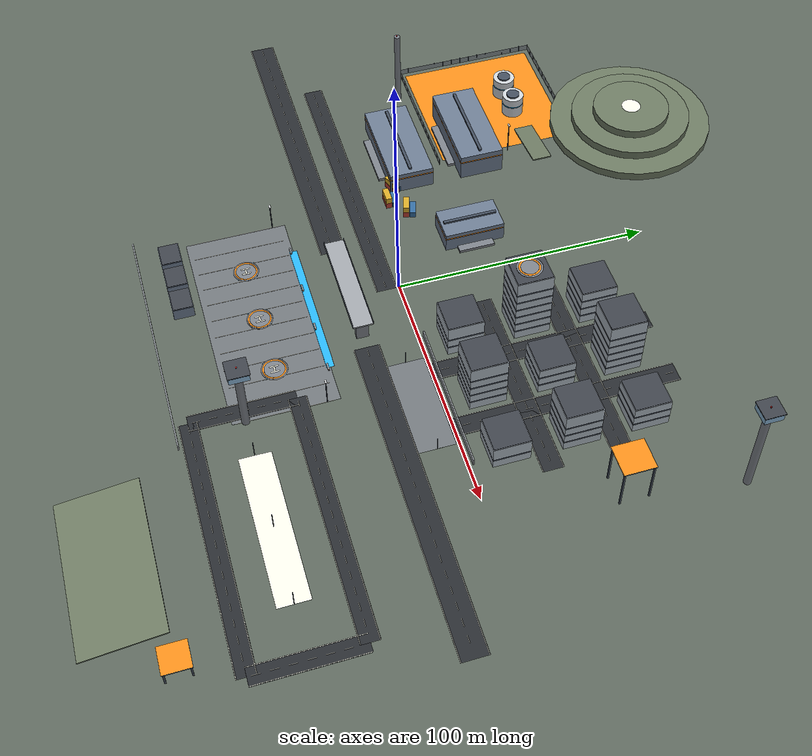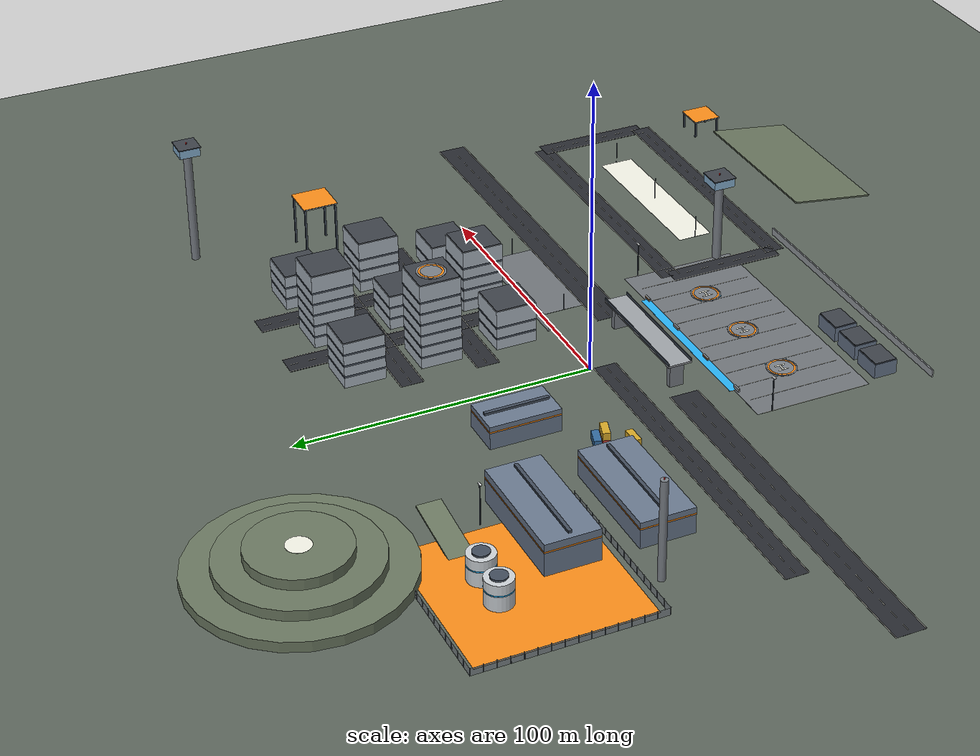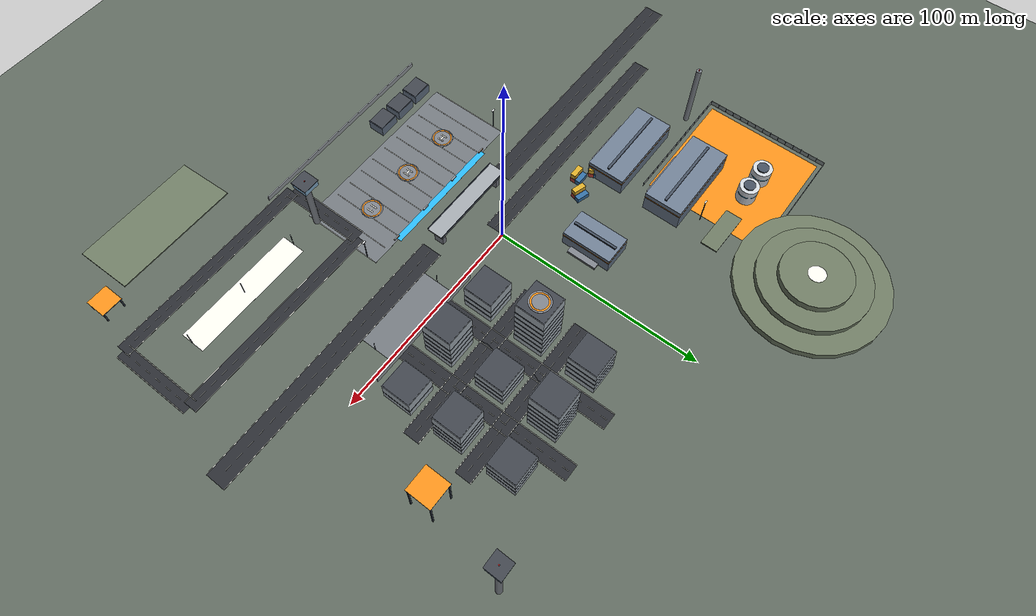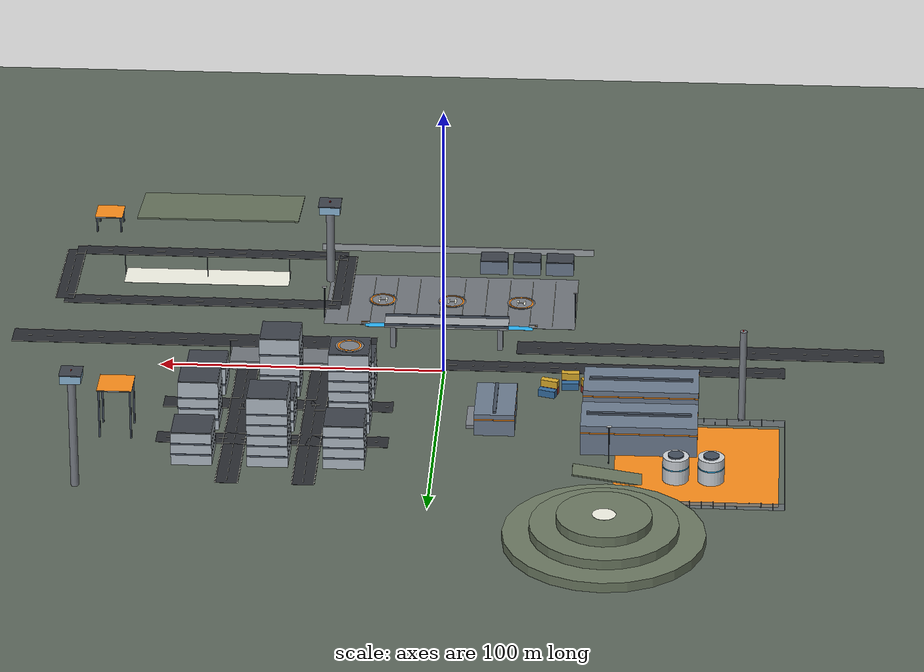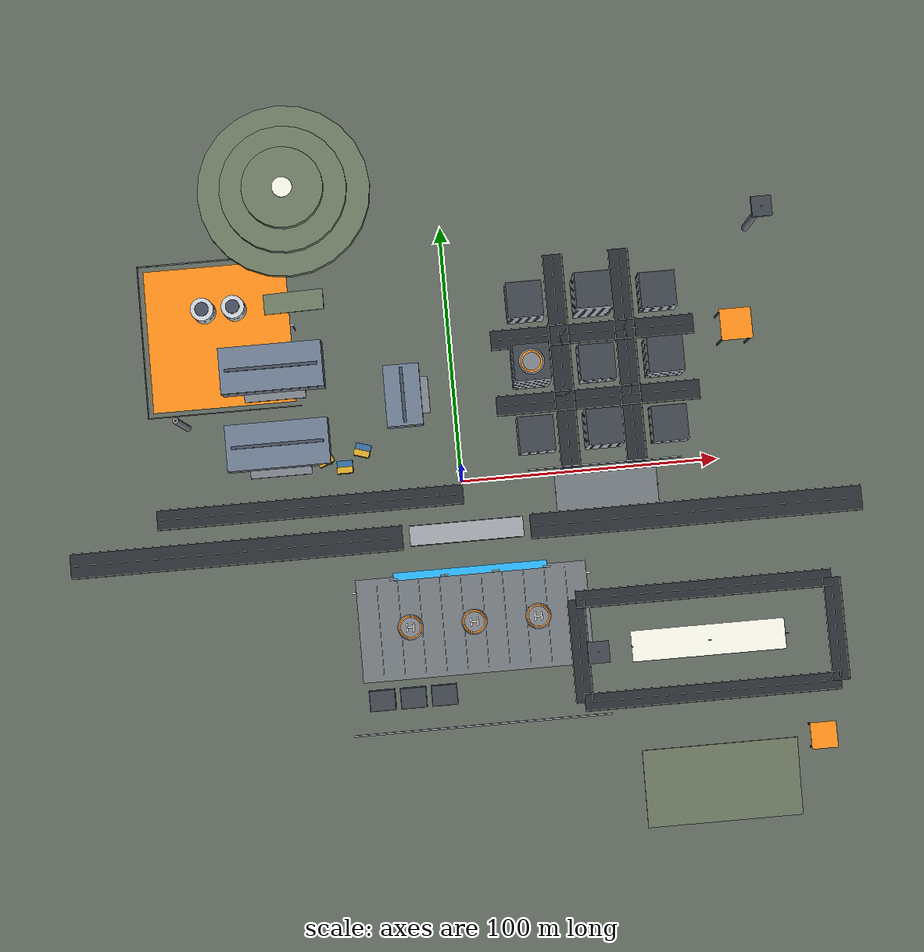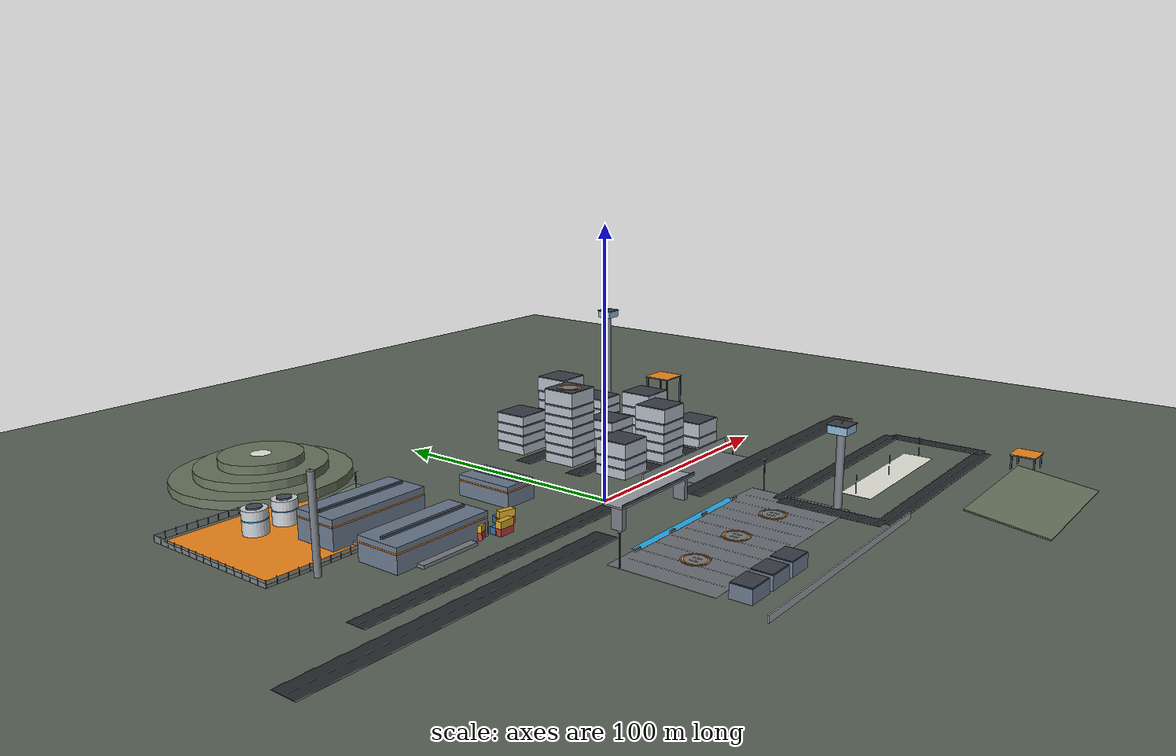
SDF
<?xml version="1.0" ?>
<!-- GENERATED by sim/worlds/autonomous_city.py - edit the generator, not this file.
     Physics/plugins, lighting and agents are injected at load time by simapi (markers below). -->
<sdf version="1.9">
  <world name="autonomous_city">
    <!-- @physics -->
    <gravity>0 0 -9.8</gravity>
    <spherical_coordinates>
      <surface_model>EARTH_WGS84</surface_model><world_frame_orientation>ENU</world_frame_orientation>
      <latitude_deg>47.3977</latitude_deg><longitude_deg>8.5456</longitude_deg><elevation>488.0</elevation><heading_deg>0</heading_deg>
    </spherical_coordinates>
    <!-- @lighting -->

    <model name="ground"><static>true</static><link name="link">
      <collision name="collision"><geometry><plane><normal>0 0 1</normal><size>600 600</size></plane></geometry>
        <surface><friction><ode><mu>100</mu><mu2>50</mu2></ode></friction></surface></collision>
      <visual name="visual"><geometry><plane><normal>0 0 1</normal><size>600 600</size></plane></geometry><material><ambient>0.36 0.40 0.36 1</ambient><diffuse>0.36 0.40 0.36 1</diffuse><specular>0.15 0.15 0.15 1</specular></material></visual>
    </link></model>
    <model name="ops_apron">
      <static>true</static>
      <pose>0 -55 0 0 0 0.0</pose>
      <link name="link">
        <visual name="slab"><pose>0 0 0.015 0 0 0</pose><geometry><box><size>90.000 40.000 0.030</size></box></geometry><material><ambient>0.44 0.46 0.48 1</ambient><diffuse>0.44 0.46 0.48 1</diffuse><specular>0.15 0.15 0.15 1</specular></material></visual>
        <visual name="bay0"><pose>-45.00 0 0.035 0 0 0</pose><geometry><box><size>0.200 36.000 0.010</size></box></geometry><material><ambient>0.95 0.95 0.90 1</ambient><diffuse>0.95 0.95 0.90 1</diffuse><specular>0.15 0.15 0.15 1</specular></material></visual>
        <visual name="bay1"><pose>-36.82 0 0.035 0 0 0</pose><geometry><box><size>0.200 36.000 0.010</size></box></geometry><material><ambient>0.95 0.95 0.90 1</ambient><diffuse>0.95 0.95 0.90 1</diffuse><specular>0.15 0.15 0.15 1</specular></material></visual>
        <visual name="bay2"><pose>-28.64 0 0.035 0 0 0</pose><geometry><box><size>0.200 36.000 0.010</size></box></geometry><material><ambient>0.95 0.95 0.90 1</ambient><diffuse>0.95 0.95 0.90 1</diffuse><specular>0.15 0.15 0.15 1</specular></material></visual>
        <visual name="bay3"><pose>-20.45 0 0.035 0 0 0</pose><geometry><box><size>0.200 36.000 0.010</size></box></geometry><material><ambient>0.95 0.95 0.90 1</ambient><diffuse>0.95 0.95 0.90 1</diffuse><specular>0.15 0.15 0.15 1</specular></material></visual>
        <visual name="bay4"><pose>-12.27 0 0.035 0 0 0</pose><geometry><box><size>0.200 36.000 0.010</size></box></geometry><material><ambient>0.95 0.95 0.90 1</ambient><diffuse>0.95 0.95 0.90 1</diffuse><specular>0.15 0.15 0.15 1</specular></material></visual>
        <visual name="bay5"><pose>-4.09 0 0.035 0 0 0</pose><geometry><box><size>0.200 36.000 0.010</size></box></geometry><material><ambient>0.95 0.95 0.90 1</ambient><diffuse>0.95 0.95 0.90 1</diffuse><specular>0.15 0.15 0.15 1</specular></material></visual>
        <visual name="bay6"><pose>4.09 0 0.035 0 0 0</pose><geometry><box><size>0.200 36.000 0.010</size></box></geometry><material><ambient>0.95 0.95 0.90 1</ambient><diffuse>0.95 0.95 0.90 1</diffuse><specular>0.15 0.15 0.15 1</specular></material></visual>
        <visual name="bay7"><pose>12.27 0 0.035 0 0 0</pose><geometry><box><size>0.200 36.000 0.010</size></box></geometry><material><ambient>0.95 0.95 0.90 1</ambient><diffuse>0.95 0.95 0.90 1</diffuse><specular>0.15 0.15 0.15 1</specular></material></visual>
        <visual name="bay8"><pose>20.45 0 0.035 0 0 0</pose><geometry><box><size>0.200 36.000 0.010</size></box></geometry><material><ambient>0.95 0.95 0.90 1</ambient><diffuse>0.95 0.95 0.90 1</diffuse><specular>0.15 0.15 0.15 1</specular></material></visual>
        <visual name="bay9"><pose>28.64 0 0.035 0 0 0</pose><geometry><box><size>0.200 36.000 0.010</size></box></geometry><material><ambient>0.95 0.95 0.90 1</ambient><diffuse>0.95 0.95 0.90 1</diffuse><specular>0.15 0.15 0.15 1</specular></material></visual>
        <visual name="bay10"><pose>36.82 0 0.035 0 0 0</pose><geometry><box><size>0.200 36.000 0.010</size></box></geometry><material><ambient>0.95 0.95 0.90 1</ambient><diffuse>0.95 0.95 0.90 1</diffuse><specular>0.15 0.15 0.15 1</specular></material></visual>
        <visual name="bay11"><pose>45.00 0 0.035 0 0 0</pose><geometry><box><size>0.200 36.000 0.010</size></box></geometry><material><ambient>0.95 0.95 0.90 1</ambient><diffuse>0.95 0.95 0.90 1</diffuse><specular>0.15 0.15 0.15 1</specular></material></visual>
      </link>
    </model>
    <model name="pad_alpha">
      <static>true</static>
      <pose>-25 -55 0 0 0 0</pose>
      <link name="link">
        <visual name="pad"><pose>0 0 0.06 0 0 0</pose><geometry><cylinder><radius>5.000</radius><length>0.120</length></cylinder></geometry><material><ambient>0.48 0.50 0.53 1</ambient><diffuse>0.48 0.50 0.53 1</diffuse><specular>0.15 0.15 0.15 1</specular></material></visual>
        <collision name="pad_c"><pose>0 0 0.06 0 0 0</pose><geometry><cylinder><radius>5.000</radius><length>0.120</length></cylinder></geometry></collision>
        <visual name="ring"><pose>0 0 0.13 0 0 0</pose><geometry><cylinder><radius>4.500</radius><length>0.020</length></cylinder></geometry><material><ambient>0.98 0.55 0.10 1</ambient><diffuse>0.98 0.55 0.10 1</diffuse><specular>0.15 0.15 0.15 1</specular></material></visual>
        <visual name="inner"><pose>0 0 0.135 0 0 0</pose><geometry><cylinder><radius>3.900</radius><length>0.030</length></cylinder></geometry><material><ambient>0.48 0.50 0.53 1</ambient><diffuse>0.48 0.50 0.53 1</diffuse><specular>0.15 0.15 0.15 1</specular></material></visual>
        <visual name="h1"><pose>-1.25 0 0.15 0 0 0</pose><geometry><box><size>0.600 3.500 0.020</size></box></geometry><material><ambient>0.95 0.95 0.90 1</ambient><diffuse>0.95 0.95 0.90 1</diffuse><specular>0.15 0.15 0.15 1</specular></material></visual>
        <visual name="h2"><pose>1.25 0 0.15 0 0 0</pose><geometry><box><size>0.600 3.500 0.020</size></box></geometry><material><ambient>0.95 0.95 0.90 1</ambient><diffuse>0.95 0.95 0.90 1</diffuse><specular>0.15 0.15 0.15 1</specular></material></visual>
        <visual name="h3"><pose>0 0 0.15 0 0 0</pose><geometry><box><size>2.500 0.600 0.020</size></box></geometry><material><ambient>0.95 0.95 0.90 1</ambient><diffuse>0.95 0.95 0.90 1</diffuse><specular>0.15 0.15 0.15 1</specular></material></visual>
        <visual name="lamp0"><pose>3.71 3.71 0.15 0 0 0</pose><geometry><cylinder><radius>0.120</radius><length>0.300</length></cylinder></geometry><material><ambient>0.16 0.70 0.96 1</ambient><diffuse>0.16 0.70 0.96 1</diffuse><specular>0.15 0.15 0.15 1</specular><emissive>0.1 0.4 0.6 1</emissive></material></visual>
        <collision name="lamp0_c"><pose>3.71 3.71 0.15 0 0 0</pose><geometry><cylinder><radius>0.120</radius><length>0.300</length></cylinder></geometry></collision>
        <visual name="lamp1"><pose>-3.71 3.71 0.15 0 0 0</pose><geometry><cylinder><radius>0.120</radius><length>0.300</length></cylinder></geometry><material><ambient>0.16 0.70 0.96 1</ambient><diffuse>0.16 0.70 0.96 1</diffuse><specular>0.15 0.15 0.15 1</specular><emissive>0.1 0.4 0.6 1</emissive></material></visual>
        <collision name="lamp1_c"><pose>-3.71 3.71 0.15 0 0 0</pose><geometry><cylinder><radius>0.120</radius><length>0.300</length></cylinder></geometry></collision>
        <visual name="lamp2"><pose>-3.71 -3.71 0.15 0 0 0</pose><geometry><cylinder><radius>0.120</radius><length>0.300</length></cylinder></geometry><material><ambient>0.16 0.70 0.96 1</ambient><diffuse>0.16 0.70 0.96 1</diffuse><specular>0.15 0.15 0.15 1</specular><emissive>0.1 0.4 0.6 1</emissive></material></visual>
        <collision name="lamp2_c"><pose>-3.71 -3.71 0.15 0 0 0</pose><geometry><cylinder><radius>0.120</radius><length>0.300</length></cylinder></geometry></collision>
        <visual name="lamp3"><pose>3.71 -3.71 0.15 0 0 0</pose><geometry><cylinder><radius>0.120</radius><length>0.300</length></cylinder></geometry><material><ambient>0.16 0.70 0.96 1</ambient><diffuse>0.16 0.70 0.96 1</diffuse><specular>0.15 0.15 0.15 1</specular><emissive>0.1 0.4 0.6 1</emissive></material></visual>
        <collision name="lamp3_c"><pose>3.71 -3.71 0.15 0 0 0</pose><geometry><cylinder><radius>0.120</radius><length>0.300</length></cylinder></geometry></collision>
      </link>
    </model>
    <model name="pad_bravo">
      <static>true</static>
      <pose>0 -55 0 0 0 0</pose>
      <link name="link">
        <visual name="pad"><pose>0 0 0.06 0 0 0</pose><geometry><cylinder><radius>5.000</radius><length>0.120</length></cylinder></geometry><material><ambient>0.48 0.50 0.53 1</ambient><diffuse>0.48 0.50 0.53 1</diffuse><specular>0.15 0.15 0.15 1</specular></material></visual>
        <collision name="pad_c"><pose>0 0 0.06 0 0 0</pose><geometry><cylinder><radius>5.000</radius><length>0.120</length></cylinder></geometry></collision>
        <visual name="ring"><pose>0 0 0.13 0 0 0</pose><geometry><cylinder><radius>4.500</radius><length>0.020</length></cylinder></geometry><material><ambient>0.98 0.55 0.10 1</ambient><diffuse>0.98 0.55 0.10 1</diffuse><specular>0.15 0.15 0.15 1</specular></material></visual>
        <visual name="inner"><pose>0 0 0.135 0 0 0</pose><geometry><cylinder><radius>3.900</radius><length>0.030</length></cylinder></geometry><material><ambient>0.48 0.50 0.53 1</ambient><diffuse>0.48 0.50 0.53 1</diffuse><specular>0.15 0.15 0.15 1</specular></material></visual>
        <visual name="h1"><pose>-1.25 0 0.15 0 0 0</pose><geometry><box><size>0.600 3.500 0.020</size></box></geometry><material><ambient>0.95 0.95 0.90 1</ambient><diffuse>0.95 0.95 0.90 1</diffuse><specular>0.15 0.15 0.15 1</specular></material></visual>
        <visual name="h2"><pose>1.25 0 0.15 0 0 0</pose><geometry><box><size>0.600 3.500 0.020</size></box></geometry><material><ambient>0.95 0.95 0.90 1</ambient><diffuse>0.95 0.95 0.90 1</diffuse><specular>0.15 0.15 0.15 1</specular></material></visual>
        <visual name="h3"><pose>0 0 0.15 0 0 0</pose><geometry><box><size>2.500 0.600 0.020</size></box></geometry><material><ambient>0.95 0.95 0.90 1</ambient><diffuse>0.95 0.95 0.90 1</diffuse><specular>0.15 0.15 0.15 1</specular></material></visual>
        <visual name="lamp0"><pose>3.71 3.71 0.15 0 0 0</pose><geometry><cylinder><radius>0.120</radius><length>0.300</length></cylinder></geometry><material><ambient>0.16 0.70 0.96 1</ambient><diffuse>0.16 0.70 0.96 1</diffuse><specular>0.15 0.15 0.15 1</specular><emissive>0.1 0.4 0.6 1</emissive></material></visual>
        <collision name="lamp0_c"><pose>3.71 3.71 0.15 0 0 0</pose><geometry><cylinder><radius>0.120</radius><length>0.300</length></cylinder></geometry></collision>
        <visual name="lamp1"><pose>-3.71 3.71 0.15 0 0 0</pose><geometry><cylinder><radius>0.120</radius><length>0.300</length></cylinder></geometry><material><ambient>0.16 0.70 0.96 1</ambient><diffuse>0.16 0.70 0.96 1</diffuse><specular>0.15 0.15 0.15 1</specular><emissive>0.1 0.4 0.6 1</emissive></material></visual>
        <collision name="lamp1_c"><pose>-3.71 3.71 0.15 0 0 0</pose><geometry><cylinder><radius>0.120</radius><length>0.300</length></cylinder></geometry></collision>
        <visual name="lamp2"><pose>-3.71 -3.71 0.15 0 0 0</pose><geometry><cylinder><radius>0.120</radius><length>0.300</length></cylinder></geometry><material><ambient>0.16 0.70 0.96 1</ambient><diffuse>0.16 0.70 0.96 1</diffuse><specular>0.15 0.15 0.15 1</specular><emissive>0.1 0.4 0.6 1</emissive></material></visual>
        <collision name="lamp2_c"><pose>-3.71 -3.71 0.15 0 0 0</pose><geometry><cylinder><radius>0.120</radius><length>0.300</length></cylinder></geometry></collision>
        <visual name="lamp3"><pose>3.71 -3.71 0.15 0 0 0</pose><geometry><cylinder><radius>0.120</radius><length>0.300</length></cylinder></geometry><material><ambient>0.16 0.70 0.96 1</ambient><diffuse>0.16 0.70 0.96 1</diffuse><specular>0.15 0.15 0.15 1</specular><emissive>0.1 0.4 0.6 1</emissive></material></visual>
        <collision name="lamp3_c"><pose>3.71 -3.71 0.15 0 0 0</pose><geometry><cylinder><radius>0.120</radius><length>0.300</length></cylinder></geometry></collision>
      </link>
    </model>
    <model name="pad_charlie">
      <static>true</static>
      <pose>25 -55 0 0 0 0</pose>
      <link name="link">
        <visual name="pad"><pose>0 0 0.06 0 0 0</pose><geometry><cylinder><radius>5.000</radius><length>0.120</length></cylinder></geometry><material><ambient>0.48 0.50 0.53 1</ambient><diffuse>0.48 0.50 0.53 1</diffuse><specular>0.15 0.15 0.15 1</specular></material></visual>
        <collision name="pad_c"><pose>0 0 0.06 0 0 0</pose><geometry><cylinder><radius>5.000</radius><length>0.120</length></cylinder></geometry></collision>
        <visual name="ring"><pose>0 0 0.13 0 0 0</pose><geometry><cylinder><radius>4.500</radius><length>0.020</length></cylinder></geometry><material><ambient>0.98 0.55 0.10 1</ambient><diffuse>0.98 0.55 0.10 1</diffuse><specular>0.15 0.15 0.15 1</specular></material></visual>
        <visual name="inner"><pose>0 0 0.135 0 0 0</pose><geometry><cylinder><radius>3.900</radius><length>0.030</length></cylinder></geometry><material><ambient>0.48 0.50 0.53 1</ambient><diffuse>0.48 0.50 0.53 1</diffuse><specular>0.15 0.15 0.15 1</specular></material></visual>
        <visual name="h1"><pose>-1.25 0 0.15 0 0 0</pose><geometry><box><size>0.600 3.500 0.020</size></box></geometry><material><ambient>0.95 0.95 0.90 1</ambient><diffuse>0.95 0.95 0.90 1</diffuse><specular>0.15 0.15 0.15 1</specular></material></visual>
        <visual name="h2"><pose>1.25 0 0.15 0 0 0</pose><geometry><box><size>0.600 3.500 0.020</size></box></geometry><material><ambient>0.95 0.95 0.90 1</ambient><diffuse>0.95 0.95 0.90 1</diffuse><specular>0.15 0.15 0.15 1</specular></material></visual>
        <visual name="h3"><pose>0 0 0.15 0 0 0</pose><geometry><box><size>2.500 0.600 0.020</size></box></geometry><material><ambient>0.95 0.95 0.90 1</ambient><diffuse>0.95 0.95 0.90 1</diffuse><specular>0.15 0.15 0.15 1</specular></material></visual>
        <visual name="lamp0"><pose>3.71 3.71 0.15 0 0 0</pose><geometry><cylinder><radius>0.120</radius><length>0.300</length></cylinder></geometry><material><ambient>0.16 0.70 0.96 1</ambient><diffuse>0.16 0.70 0.96 1</diffuse><specular>0.15 0.15 0.15 1</specular><emissive>0.1 0.4 0.6 1</emissive></material></visual>
        <collision name="lamp0_c"><pose>3.71 3.71 0.15 0 0 0</pose><geometry><cylinder><radius>0.120</radius><length>0.300</length></cylinder></geometry></collision>
        <visual name="lamp1"><pose>-3.71 3.71 0.15 0 0 0</pose><geometry><cylinder><radius>0.120</radius><length>0.300</length></cylinder></geometry><material><ambient>0.16 0.70 0.96 1</ambient><diffuse>0.16 0.70 0.96 1</diffuse><specular>0.15 0.15 0.15 1</specular><emissive>0.1 0.4 0.6 1</emissive></material></visual>
        <collision name="lamp1_c"><pose>-3.71 3.71 0.15 0 0 0</pose><geometry><cylinder><radius>0.120</radius><length>0.300</length></cylinder></geometry></collision>
        <visual name="lamp2"><pose>-3.71 -3.71 0.15 0 0 0</pose><geometry><cylinder><radius>0.120</radius><length>0.300</length></cylinder></geometry><material><ambient>0.16 0.70 0.96 1</ambient><diffuse>0.16 0.70 0.96 1</diffuse><specular>0.15 0.15 0.15 1</specular><emissive>0.1 0.4 0.6 1</emissive></material></visual>
        <collision name="lamp2_c"><pose>-3.71 -3.71 0.15 0 0 0</pose><geometry><cylinder><radius>0.120</radius><length>0.300</length></cylinder></geometry></collision>
        <visual name="lamp3"><pose>3.71 -3.71 0.15 0 0 0</pose><geometry><cylinder><radius>0.120</radius><length>0.300</length></cylinder></geometry><material><ambient>0.16 0.70 0.96 1</ambient><diffuse>0.16 0.70 0.96 1</diffuse><specular>0.15 0.15 0.15 1</specular><emissive>0.1 0.4 0.6 1</emissive></material></visual>
        <collision name="lamp3_c"><pose>3.71 -3.71 0.15 0 0 0</pose><geometry><cylinder><radius>0.120</radius><length>0.300</length></cylinder></geometry></collision>
      </link>
    </model>
    <model name="ops_tower">
      <static>true</static>
      <pose>45 -70 0 0 0 0</pose>
      <link name="link">
        <visual name="mast"><pose>0 0 14.0 0 0 0</pose><geometry><cylinder><radius>1.500</radius><length>28.000</length></cylinder></geometry><material><ambient>0.48 0.50 0.53 1</ambient><diffuse>0.48 0.50 0.53 1</diffuse><specular>0.15 0.15 0.15 1</specular></material></visual>
        <collision name="mast_c"><pose>0 0 14.0 0 0 0</pose><geometry><cylinder><radius>1.500</radius><length>28.000</length></cylinder></geometry></collision>
        <visual name="cabin"><pose>0 0 29.5 0 0 0</pose><geometry><box><size>7.500 7.500 3.000</size></box></geometry><material><ambient>0.55 0.72 0.85 0.9</ambient><diffuse>0.55 0.72 0.85 0.9</diffuse><specular>0.15 0.15 0.15 1</specular></material></visual>
        <collision name="cabin_c"><pose>0 0 29.5 0 0 0</pose><geometry><box><size>7.500 7.500 3.000</size></box></geometry></collision>
        <visual name="cabin_roof"><pose>0 0 31.15 0 0 0</pose><geometry><box><size>8.100 8.100 0.300</size></box></geometry><material><ambient>0.24 0.26 0.29 1</ambient><diffuse>0.24 0.26 0.29 1</diffuse><specular>0.15 0.15 0.15 1</specular></material></visual>
        <collision name="cabin_roof_c"><pose>0 0 31.15 0 0 0</pose><geometry><box><size>8.100 8.100 0.300</size></box></geometry></collision>
        <visual name="beacon"><pose>0 0 31.6 0 0 0</pose><geometry><cylinder><radius>0.250</radius><length>0.500</length></cylinder></geometry><material><ambient>0.95 0.20 0.20 1</ambient><diffuse>0.95 0.20 0.20 1</diffuse><specular>0.15 0.15 0.15 1</specular><emissive>0.6 0.1 0.1 1</emissive></material></visual>
      </link>
    </model>
    <model name="service_bay_01">
      <static>true</static>
      <pose>-38 -82 0 0 0 0.0</pose>
      <link name="link">
        <visual name="core"><pose>0 0 2.5 0 0 0</pose><geometry><box><size>10.000 8.000 5.000</size></box></geometry><material><ambient>0.42 0.48 0.56 1</ambient><diffuse>0.42 0.48 0.56 1</diffuse><specular>0.15 0.15 0.15 1</specular></material></visual>
        <collision name="core_c"><pose>0 0 2.5 0 0 0</pose><geometry><box><size>10.000 8.000 5.000</size></box></geometry></collision>
        <visual name="roof"><pose>0 0 5.15 0 0 0</pose><geometry><box><size>9.600 7.600 0.300</size></box></geometry><material><ambient>0.24 0.26 0.29 1</ambient><diffuse>0.24 0.26 0.29 1</diffuse><specular>0.15 0.15 0.15 1</specular></material></visual>
        <collision name="roof_c"><pose>0 0 5.15 0 0 0</pose><geometry><box><size>9.600 7.600 0.300</size></box></geometry></collision>
      </link>
    </model>
    <model name="service_bay_02">
      <static>true</static>
      <pose>-26 -82 0 0 0 0.0</pose>
      <link name="link">
        <visual name="core"><pose>0 0 2.5 0 0 0</pose><geometry><box><size>10.000 8.000 5.000</size></box></geometry><material><ambient>0.42 0.48 0.56 1</ambient><diffuse>0.42 0.48 0.56 1</diffuse><specular>0.15 0.15 0.15 1</specular></material></visual>
        <collision name="core_c"><pose>0 0 2.5 0 0 0</pose><geometry><box><size>10.000 8.000 5.000</size></box></geometry></collision>
        <visual name="roof"><pose>0 0 5.15 0 0 0</pose><geometry><box><size>9.600 7.600 0.300</size></box></geometry><material><ambient>0.24 0.26 0.29 1</ambient><diffuse>0.24 0.26 0.29 1</diffuse><specular>0.15 0.15 0.15 1</specular></material></visual>
        <collision name="roof_c"><pose>0 0 5.15 0 0 0</pose><geometry><box><size>9.600 7.600 0.300</size></box></geometry></collision>
      </link>
    </model>
    <model name="service_bay_03">
      <static>true</static>
      <pose>-14 -82 0 0 0 0.0</pose>
      <link name="link">
        <visual name="core"><pose>0 0 2.5 0 0 0</pose><geometry><box><size>10.000 8.000 5.000</size></box></geometry><material><ambient>0.42 0.48 0.56 1</ambient><diffuse>0.42 0.48 0.56 1</diffuse><specular>0.15 0.15 0.15 1</specular></material></visual>
        <collision name="core_c"><pose>0 0 2.5 0 0 0</pose><geometry><box><size>10.000 8.000 5.000</size></box></geometry></collision>
        <visual name="roof"><pose>0 0 5.15 0 0 0</pose><geometry><box><size>9.600 7.600 0.300</size></box></geometry><material><ambient>0.24 0.26 0.29 1</ambient><diffuse>0.24 0.26 0.29 1</diffuse><specular>0.15 0.15 0.15 1</specular></material></visual>
        <collision name="roof_c"><pose>0 0 5.15 0 0 0</pose><geometry><box><size>9.600 7.600 0.300</size></box></geometry></collision>
      </link>
    </model>
    <model name="launch_zone">
      <static>true</static>
      <pose>0 -35 0 0 0 0.0</pose>
      <link name="link">
        <visual name="mark"><pose>0 0 0.05 0 0 0</pose><geometry><box><size>60.000 3.000 0.015</size></box></geometry><material><ambient>0.16 0.70 0.96 1</ambient><diffuse>0.16 0.70 0.96 1</diffuse><specular>0.15 0.15 0.15 1</specular></material></visual>
      </link>
    </model>
    <model name="ops_mast_01">
      <static>true</static>
      <pose>-45 -40 0 0 0 0</pose>
      <link name="link">
        <visual name="mast"><pose>0 0 6.0 0 0 0</pose><geometry><cylinder><radius>0.180</radius><length>12.000</length></cylinder></geometry><material><ambient>0.26 0.30 0.36 1</ambient><diffuse>0.26 0.30 0.36 1</diffuse><specular>0.15 0.15 0.15 1</specular></material></visual>
        <collision name="mast_c"><pose>0 0 6.0 0 0 0</pose><geometry><cylinder><radius>0.180</radius><length>12.000</length></cylinder></geometry></collision>
        <visual name="head"><pose>0 0 12.15 0 0 0</pose><geometry><box><size>1.600 0.600 0.300</size></box></geometry><material><ambient>0.92 0.93 0.94 1</ambient><diffuse>0.92 0.93 0.94 1</diffuse><specular>0.15 0.15 0.15 1</specular><emissive>0.5 0.5 0.45 1</emissive></material></visual>
      </link>
    </model>
    <model name="ops_mast_02">
      <static>true</static>
      <pose>45 -40 0 0 0 0</pose>
      <link name="link">
        <visual name="mast"><pose>0 0 6.0 0 0 0</pose><geometry><cylinder><radius>0.180</radius><length>12.000</length></cylinder></geometry><material><ambient>0.26 0.30 0.36 1</ambient><diffuse>0.26 0.30 0.36 1</diffuse><specular>0.15 0.15 0.15 1</specular></material></visual>
        <collision name="mast_c"><pose>0 0 6.0 0 0 0</pose><geometry><cylinder><radius>0.180</radius><length>12.000</length></cylinder></geometry></collision>
        <visual name="head"><pose>0 0 12.15 0 0 0</pose><geometry><box><size>1.600 0.600 0.300</size></box></geometry><material><ambient>0.92 0.93 0.94 1</ambient><diffuse>0.92 0.93 0.94 1</diffuse><specular>0.15 0.15 0.15 1</specular><emissive>0.5 0.5 0.45 1</emissive></material></visual>
      </link>
    </model>
    <model name="ops_wall_s">
      <static>true</static>
      <pose>0 -95 0 0 0 0.0</pose>
      <link name="link">
        <visual name="wall"><pose>0 0 1.25 0 0 0</pose><geometry><box><size>100.000 0.500 2.500</size></box></geometry><material><ambient>0.62 0.64 0.66 1</ambient><diffuse>0.62 0.64 0.66 1</diffuse><specular>0.15 0.15 0.15 1</specular></material></visual>
        <collision name="wall_c"><pose>0 0 1.25 0 0 0</pose><geometry><box><size>100.000 0.500 2.500</size></box></geometry></collision>
      </link>
    </model>
    <model name="ops_barrier_01">
      <static>true</static>
      <pose>-30 -36 0 0 0 0.0</pose>
      <link name="link">
        <visual name="base"><pose>0 0 0.45 0 0 0</pose><geometry><box><size>3.000 0.600 0.900</size></box></geometry><material><ambient>0.62 0.64 0.66 1</ambient><diffuse>0.62 0.64 0.66 1</diffuse><specular>0.15 0.15 0.15 1</specular></material></visual>
        <collision name="base_c"><pose>0 0 0.45 0 0 0</pose><geometry><box><size>3.000 0.600 0.900</size></box></geometry></collision>
        <visual name="stripe"><pose>0 0 0.7 0 0 0</pose><geometry><box><size>3.020 0.620 0.150</size></box></geometry><material><ambient>0.98 0.55 0.10 1</ambient><diffuse>0.98 0.55 0.10 1</diffuse><specular>0.15 0.15 0.15 1</specular></material></visual>
      </link>
    </model>
    <model name="ops_barrier_02">
      <static>true</static>
      <pose>-10 -36 0 0 0 0.0</pose>
      <link name="link">
        <visual name="base"><pose>0 0 0.45 0 0 0</pose><geometry><box><size>3.000 0.600 0.900</size></box></geometry><material><ambient>0.62 0.64 0.66 1</ambient><diffuse>0.62 0.64 0.66 1</diffuse><specular>0.15 0.15 0.15 1</specular></material></visual>
        <collision name="base_c"><pose>0 0 0.45 0 0 0</pose><geometry><box><size>3.000 0.600 0.900</size></box></geometry></collision>
        <visual name="stripe"><pose>0 0 0.7 0 0 0</pose><geometry><box><size>3.020 0.620 0.150</size></box></geometry><material><ambient>0.98 0.55 0.10 1</ambient><diffuse>0.98 0.55 0.10 1</diffuse><specular>0.15 0.15 0.15 1</specular></material></visual>
      </link>
    </model>
    <model name="ops_barrier_03">
      <static>true</static>
      <pose>10 -36 0 0 0 0.0</pose>
      <link name="link">
        <visual name="base"><pose>0 0 0.45 0 0 0</pose><geometry><box><size>3.000 0.600 0.900</size></box></geometry><material><ambient>0.62 0.64 0.66 1</ambient><diffuse>0.62 0.64 0.66 1</diffuse><specular>0.15 0.15 0.15 1</specular></material></visual>
        <collision name="base_c"><pose>0 0 0.45 0 0 0</pose><geometry><box><size>3.000 0.600 0.900</size></box></geometry></collision>
        <visual name="stripe"><pose>0 0 0.7 0 0 0</pose><geometry><box><size>3.020 0.620 0.150</size></box></geometry><material><ambient>0.98 0.55 0.10 1</ambient><diffuse>0.98 0.55 0.10 1</diffuse><specular>0.15 0.15 0.15 1</specular></material></visual>
      </link>
    </model>
    <model name="ops_barrier_04">
      <static>true</static>
      <pose>30 -36 0 0 0 0.0</pose>
      <link name="link">
        <visual name="base"><pose>0 0 0.45 0 0 0</pose><geometry><box><size>3.000 0.600 0.900</size></box></geometry><material><ambient>0.62 0.64 0.66 1</ambient><diffuse>0.62 0.64 0.66 1</diffuse><specular>0.15 0.15 0.15 1</specular></material></visual>
        <collision name="base_c"><pose>0 0 0.45 0 0 0</pose><geometry><box><size>3.000 0.600 0.900</size></box></geometry></collision>
        <visual name="stripe"><pose>0 0 0.7 0 0 0</pose><geometry><box><size>3.020 0.620 0.150</size></box></geometry><material><ambient>0.98 0.55 0.10 1</ambient><diffuse>0.98 0.55 0.10 1</diffuse><specular>0.15 0.15 0.15 1</specular></material></visual>
      </link>
    </model>
    <model name="building_01">
      <static>true</static>
      <pose>30 15 0 0 0 0.0</pose>
      <link name="link">
        <visual name="core"><pose>0 0 7.0 0 0 0</pose><geometry><box><size>14.000 14.000 14.000</size></box></geometry><material><ambient>0.70 0.74 0.78 1</ambient><diffuse>0.70 0.74 0.78 1</diffuse><specular>0.15 0.15 0.15 1</specular></material></visual>
        <collision name="core_c"><pose>0 0 7.0 0 0 0</pose><geometry><box><size>14.000 14.000 14.000</size></box></geometry></collision>
        <visual name="band1"><pose>0 0 4.00 0 0 0</pose><geometry><box><size>14.060 14.060 0.600</size></box></geometry><material><ambient>0.30 0.34 0.40 1</ambient><diffuse>0.30 0.34 0.40 1</diffuse><specular>0.15 0.15 0.15 1</specular></material></visual>
        <visual name="band2"><pose>0 0 8.00 0 0 0</pose><geometry><box><size>14.060 14.060 0.600</size></box></geometry><material><ambient>0.30 0.34 0.40 1</ambient><diffuse>0.30 0.34 0.40 1</diffuse><specular>0.15 0.15 0.15 1</specular></material></visual>
        <visual name="roof"><pose>0 0 14.15 0 0 0</pose><geometry><box><size>13.600 13.600 0.300</size></box></geometry><material><ambient>0.24 0.26 0.29 1</ambient><diffuse>0.24 0.26 0.29 1</diffuse><specular>0.15 0.15 0.15 1</specular></material></visual>
        <collision name="roof_c"><pose>0 0 14.15 0 0 0</pose><geometry><box><size>13.600 13.600 0.300</size></box></geometry></collision>
      </link>
    </model>
    <model name="building_02">
      <static>true</static>
      <pose>56 15 0 0 0 0.0</pose>
      <link name="link">
        <visual name="core"><pose>0 0 11.0 0 0 0</pose><geometry><box><size>14.000 14.000 22.000</size></box></geometry><material><ambient>0.70 0.74 0.78 1</ambient><diffuse>0.70 0.74 0.78 1</diffuse><specular>0.15 0.15 0.15 1</specular></material></visual>
        <collision name="core_c"><pose>0 0 11.0 0 0 0</pose><geometry><box><size>14.000 14.000 22.000</size></box></geometry></collision>
        <visual name="band1"><pose>0 0 4.00 0 0 0</pose><geometry><box><size>14.060 14.060 0.600</size></box></geometry><material><ambient>0.30 0.34 0.40 1</ambient><diffuse>0.30 0.34 0.40 1</diffuse><specular>0.15 0.15 0.15 1</specular></material></visual>
        <visual name="band2"><pose>0 0 8.00 0 0 0</pose><geometry><box><size>14.060 14.060 0.600</size></box></geometry><material><ambient>0.30 0.34 0.40 1</ambient><diffuse>0.30 0.34 0.40 1</diffuse><specular>0.15 0.15 0.15 1</specular></material></visual>
        <visual name="band3"><pose>0 0 12.00 0 0 0</pose><geometry><box><size>14.060 14.060 0.600</size></box></geometry><material><ambient>0.30 0.34 0.40 1</ambient><diffuse>0.30 0.34 0.40 1</diffuse><specular>0.15 0.15 0.15 1</specular></material></visual>
        <visual name="band4"><pose>0 0 16.00 0 0 0</pose><geometry><box><size>14.060 14.060 0.600</size></box></geometry><material><ambient>0.30 0.34 0.40 1</ambient><diffuse>0.30 0.34 0.40 1</diffuse><specular>0.15 0.15 0.15 1</specular></material></visual>
        <visual name="roof"><pose>0 0 22.15 0 0 0</pose><geometry><box><size>13.600 13.600 0.300</size></box></geometry><material><ambient>0.24 0.26 0.29 1</ambient><diffuse>0.24 0.26 0.29 1</diffuse><specular>0.15 0.15 0.15 1</specular></material></visual>
        <collision name="roof_c"><pose>0 0 22.15 0 0 0</pose><geometry><box><size>13.600 13.600 0.300</size></box></geometry></collision>
      </link>
    </model>
    <model name="building_03">
      <static>true</static>
      <pose>82 15 0 0 0 0.0</pose>
      <link name="link">
        <visual name="core"><pose>0 0 5.0 0 0 0</pose><geometry><box><size>14.000 14.000 10.000</size></box></geometry><material><ambient>0.70 0.74 0.78 1</ambient><diffuse>0.70 0.74 0.78 1</diffuse><specular>0.15 0.15 0.15 1</specular></material></visual>
        <collision name="core_c"><pose>0 0 5.0 0 0 0</pose><geometry><box><size>14.000 14.000 10.000</size></box></geometry></collision>
        <visual name="band1"><pose>0 0 4.00 0 0 0</pose><geometry><box><size>14.060 14.060 0.600</size></box></geometry><material><ambient>0.30 0.34 0.40 1</ambient><diffuse>0.30 0.34 0.40 1</diffuse><specular>0.15 0.15 0.15 1</specular></material></visual>
        <visual name="roof"><pose>0 0 10.15 0 0 0</pose><geometry><box><size>13.600 13.600 0.300</size></box></geometry><material><ambient>0.24 0.26 0.29 1</ambient><diffuse>0.24 0.26 0.29 1</diffuse><specular>0.15 0.15 0.15 1</specular></material></visual>
        <collision name="roof_c"><pose>0 0 10.15 0 0 0</pose><geometry><box><size>13.600 13.600 0.300</size></box></geometry></collision>
      </link>
    </model>
    <model name="building_04">
      <static>true</static>
      <pose>30 41 0 0 0 0.0</pose>
      <link name="link">
        <visual name="core"><pose>0 0 15.0 0 0 0</pose><geometry><box><size>14.000 14.000 30.000</size></box></geometry><material><ambient>0.70 0.74 0.78 1</ambient><diffuse>0.70 0.74 0.78 1</diffuse><specular>0.15 0.15 0.15 1</specular></material></visual>
        <collision name="core_c"><pose>0 0 15.0 0 0 0</pose><geometry><box><size>14.000 14.000 30.000</size></box></geometry></collision>
        <visual name="band1"><pose>0 0 4.00 0 0 0</pose><geometry><box><size>14.060 14.060 0.600</size></box></geometry><material><ambient>0.30 0.34 0.40 1</ambient><diffuse>0.30 0.34 0.40 1</diffuse><specular>0.15 0.15 0.15 1</specular></material></visual>
        <visual name="band2"><pose>0 0 8.00 0 0 0</pose><geometry><box><size>14.060 14.060 0.600</size></box></geometry><material><ambient>0.30 0.34 0.40 1</ambient><diffuse>0.30 0.34 0.40 1</diffuse><specular>0.15 0.15 0.15 1</specular></material></visual>
        <visual name="band3"><pose>0 0 12.00 0 0 0</pose><geometry><box><size>14.060 14.060 0.600</size></box></geometry><material><ambient>0.30 0.34 0.40 1</ambient><diffuse>0.30 0.34 0.40 1</diffuse><specular>0.15 0.15 0.15 1</specular></material></visual>
        <visual name="band4"><pose>0 0 16.00 0 0 0</pose><geometry><box><size>14.060 14.060 0.600</size></box></geometry><material><ambient>0.30 0.34 0.40 1</ambient><diffuse>0.30 0.34 0.40 1</diffuse><specular>0.15 0.15 0.15 1</specular></material></visual>
        <visual name="band5"><pose>0 0 20.00 0 0 0</pose><geometry><box><size>14.060 14.060 0.600</size></box></geometry><material><ambient>0.30 0.34 0.40 1</ambient><diffuse>0.30 0.34 0.40 1</diffuse><specular>0.15 0.15 0.15 1</specular></material></visual>
        <visual name="band6"><pose>0 0 24.00 0 0 0</pose><geometry><box><size>14.060 14.060 0.600</size></box></geometry><material><ambient>0.30 0.34 0.40 1</ambient><diffuse>0.30 0.34 0.40 1</diffuse><specular>0.15 0.15 0.15 1</specular></material></visual>
        <visual name="roof"><pose>0 0 30.15 0 0 0</pose><geometry><box><size>13.600 13.600 0.300</size></box></geometry><material><ambient>0.24 0.26 0.29 1</ambient><diffuse>0.24 0.26 0.29 1</diffuse><specular>0.15 0.15 0.15 1</specular></material></visual>
        <collision name="roof_c"><pose>0 0 30.15 0 0 0</pose><geometry><box><size>13.600 13.600 0.300</size></box></geometry></collision>
        <visual name="helipad"><pose>0 0 30.33 0 0 0</pose><geometry><cylinder><radius>4.900</radius><length>0.050</length></cylinder></geometry><material><ambient>0.48 0.50 0.53 1</ambient><diffuse>0.48 0.50 0.53 1</diffuse><specular>0.15 0.15 0.15 1</specular></material></visual>
        <visual name="helipad_ring"><pose>0 0 30.34 0 0 0</pose><geometry><cylinder><radius>4.165</radius><length>0.060</length></cylinder></geometry><material><ambient>0.98 0.55 0.10 1</ambient><diffuse>0.98 0.55 0.10 1</diffuse><specular>0.15 0.15 0.15 1</specular></material></visual>
        <visual name="helipad_core"><pose>0 0 30.35 0 0 0</pose><geometry><cylinder><radius>3.430</radius><length>0.070</length></cylinder></geometry><material><ambient>0.48 0.50 0.53 1</ambient><diffuse>0.48 0.50 0.53 1</diffuse><specular>0.15 0.15 0.15 1</specular></material></visual>
      </link>
    </model>
    <model name="building_05">
      <static>true</static>
      <pose>56 41 0 0 0 0.0</pose>
      <link name="link">
        <visual name="core"><pose>0 0 6.0 0 0 0</pose><geometry><box><size>14.000 14.000 12.000</size></box></geometry><material><ambient>0.70 0.74 0.78 1</ambient><diffuse>0.70 0.74 0.78 1</diffuse><specular>0.15 0.15 0.15 1</specular></material></visual>
        <collision name="core_c"><pose>0 0 6.0 0 0 0</pose><geometry><box><size>14.000 14.000 12.000</size></box></geometry></collision>
        <visual name="band1"><pose>0 0 4.00 0 0 0</pose><geometry><box><size>14.060 14.060 0.600</size></box></geometry><material><ambient>0.30 0.34 0.40 1</ambient><diffuse>0.30 0.34 0.40 1</diffuse><specular>0.15 0.15 0.15 1</specular></material></visual>
        <visual name="band2"><pose>0 0 8.00 0 0 0</pose><geometry><box><size>14.060 14.060 0.600</size></box></geometry><material><ambient>0.30 0.34 0.40 1</ambient><diffuse>0.30 0.34 0.40 1</diffuse><specular>0.15 0.15 0.15 1</specular></material></visual>
        <visual name="roof"><pose>0 0 12.15 0 0 0</pose><geometry><box><size>13.600 13.600 0.300</size></box></geometry><material><ambient>0.24 0.26 0.29 1</ambient><diffuse>0.24 0.26 0.29 1</diffuse><specular>0.15 0.15 0.15 1</specular></material></visual>
        <collision name="roof_c"><pose>0 0 12.15 0 0 0</pose><geometry><box><size>13.600 13.600 0.300</size></box></geometry></collision>
      </link>
    </model>
    <model name="building_06">
      <static>true</static>
      <pose>82 41 0 0 0 0.0</pose>
      <link name="link">
        <visual name="core"><pose>0 0 9.0 0 0 0</pose><geometry><box><size>14.000 14.000 18.000</size></box></geometry><material><ambient>0.70 0.74 0.78 1</ambient><diffuse>0.70 0.74 0.78 1</diffuse><specular>0.15 0.15 0.15 1</specular></material></visual>
        <collision name="core_c"><pose>0 0 9.0 0 0 0</pose><geometry><box><size>14.000 14.000 18.000</size></box></geometry></collision>
        <visual name="band1"><pose>0 0 4.00 0 0 0</pose><geometry><box><size>14.060 14.060 0.600</size></box></geometry><material><ambient>0.30 0.34 0.40 1</ambient><diffuse>0.30 0.34 0.40 1</diffuse><specular>0.15 0.15 0.15 1</specular></material></visual>
        <visual name="band2"><pose>0 0 8.00 0 0 0</pose><geometry><box><size>14.060 14.060 0.600</size></box></geometry><material><ambient>0.30 0.34 0.40 1</ambient><diffuse>0.30 0.34 0.40 1</diffuse><specular>0.15 0.15 0.15 1</specular></material></visual>
        <visual name="band3"><pose>0 0 12.00 0 0 0</pose><geometry><box><size>14.060 14.060 0.600</size></box></geometry><material><ambient>0.30 0.34 0.40 1</ambient><diffuse>0.30 0.34 0.40 1</diffuse><specular>0.15 0.15 0.15 1</specular></material></visual>
        <visual name="roof"><pose>0 0 18.15 0 0 0</pose><geometry><box><size>13.600 13.600 0.300</size></box></geometry><material><ambient>0.24 0.26 0.29 1</ambient><diffuse>0.24 0.26 0.29 1</diffuse><specular>0.15 0.15 0.15 1</specular></material></visual>
        <collision name="roof_c"><pose>0 0 18.15 0 0 0</pose><geometry><box><size>13.600 13.600 0.300</size></box></geometry></collision>
      </link>
    </model>
    <model name="building_07">
      <static>true</static>
      <pose>30 67 0 0 0 0.0</pose>
      <link name="link">
        <visual name="core"><pose>0 0 8.0 0 0 0</pose><geometry><box><size>14.000 14.000 16.000</size></box></geometry><material><ambient>0.70 0.74 0.78 1</ambient><diffuse>0.70 0.74 0.78 1</diffuse><specular>0.15 0.15 0.15 1</specular></material></visual>
        <collision name="core_c"><pose>0 0 8.0 0 0 0</pose><geometry><box><size>14.000 14.000 16.000</size></box></geometry></collision>
        <visual name="band1"><pose>0 0 4.00 0 0 0</pose><geometry><box><size>14.060 14.060 0.600</size></box></geometry><material><ambient>0.30 0.34 0.40 1</ambient><diffuse>0.30 0.34 0.40 1</diffuse><specular>0.15 0.15 0.15 1</specular></material></visual>
        <visual name="band2"><pose>0 0 8.00 0 0 0</pose><geometry><box><size>14.060 14.060 0.600</size></box></geometry><material><ambient>0.30 0.34 0.40 1</ambient><diffuse>0.30 0.34 0.40 1</diffuse><specular>0.15 0.15 0.15 1</specular></material></visual>
        <visual name="band3"><pose>0 0 12.00 0 0 0</pose><geometry><box><size>14.060 14.060 0.600</size></box></geometry><material><ambient>0.30 0.34 0.40 1</ambient><diffuse>0.30 0.34 0.40 1</diffuse><specular>0.15 0.15 0.15 1</specular></material></visual>
        <visual name="roof"><pose>0 0 16.15 0 0 0</pose><geometry><box><size>13.600 13.600 0.300</size></box></geometry><material><ambient>0.24 0.26 0.29 1</ambient><diffuse>0.24 0.26 0.29 1</diffuse><specular>0.15 0.15 0.15 1</specular></material></visual>
        <collision name="roof_c"><pose>0 0 16.15 0 0 0</pose><geometry><box><size>13.600 13.600 0.300</size></box></geometry></collision>
      </link>
    </model>
    <model name="building_08">
      <static>true</static>
      <pose>56 67 0 0 0 0.0</pose>
      <link name="link">
        <visual name="core"><pose>0 0 13.0 0 0 0</pose><geometry><box><size>14.000 14.000 26.000</size></box></geometry><material><ambient>0.70 0.74 0.78 1</ambient><diffuse>0.70 0.74 0.78 1</diffuse><specular>0.15 0.15 0.15 1</specular></material></visual>
        <collision name="core_c"><pose>0 0 13.0 0 0 0</pose><geometry><box><size>14.000 14.000 26.000</size></box></geometry></collision>
        <visual name="band1"><pose>0 0 4.00 0 0 0</pose><geometry><box><size>14.060 14.060 0.600</size></box></geometry><material><ambient>0.30 0.34 0.40 1</ambient><diffuse>0.30 0.34 0.40 1</diffuse><specular>0.15 0.15 0.15 1</specular></material></visual>
        <visual name="band2"><pose>0 0 8.00 0 0 0</pose><geometry><box><size>14.060 14.060 0.600</size></box></geometry><material><ambient>0.30 0.34 0.40 1</ambient><diffuse>0.30 0.34 0.40 1</diffuse><specular>0.15 0.15 0.15 1</specular></material></visual>
        <visual name="band3"><pose>0 0 12.00 0 0 0</pose><geometry><box><size>14.060 14.060 0.600</size></box></geometry><material><ambient>0.30 0.34 0.40 1</ambient><diffuse>0.30 0.34 0.40 1</diffuse><specular>0.15 0.15 0.15 1</specular></material></visual>
        <visual name="band4"><pose>0 0 16.00 0 0 0</pose><geometry><box><size>14.060 14.060 0.600</size></box></geometry><material><ambient>0.30 0.34 0.40 1</ambient><diffuse>0.30 0.34 0.40 1</diffuse><specular>0.15 0.15 0.15 1</specular></material></visual>
        <visual name="band5"><pose>0 0 20.00 0 0 0</pose><geometry><box><size>14.060 14.060 0.600</size></box></geometry><material><ambient>0.30 0.34 0.40 1</ambient><diffuse>0.30 0.34 0.40 1</diffuse><specular>0.15 0.15 0.15 1</specular></material></visual>
        <visual name="roof"><pose>0 0 26.15 0 0 0</pose><geometry><box><size>13.600 13.600 0.300</size></box></geometry><material><ambient>0.24 0.26 0.29 1</ambient><diffuse>0.24 0.26 0.29 1</diffuse><specular>0.15 0.15 0.15 1</specular></material></visual>
        <collision name="roof_c"><pose>0 0 26.15 0 0 0</pose><geometry><box><size>13.600 13.600 0.300</size></box></geometry></collision>
      </link>
    </model>
    <model name="building_09">
      <static>true</static>
      <pose>82 67 0 0 0 0.0</pose>
      <link name="link">
        <visual name="core"><pose>0 0 6.0 0 0 0</pose><geometry><box><size>14.000 14.000 12.000</size></box></geometry><material><ambient>0.70 0.74 0.78 1</ambient><diffuse>0.70 0.74 0.78 1</diffuse><specular>0.15 0.15 0.15 1</specular></material></visual>
        <collision name="core_c"><pose>0 0 6.0 0 0 0</pose><geometry><box><size>14.000 14.000 12.000</size></box></geometry></collision>
        <visual name="band1"><pose>0 0 4.00 0 0 0</pose><geometry><box><size>14.060 14.060 0.600</size></box></geometry><material><ambient>0.30 0.34 0.40 1</ambient><diffuse>0.30 0.34 0.40 1</diffuse><specular>0.15 0.15 0.15 1</specular></material></visual>
        <visual name="band2"><pose>0 0 8.00 0 0 0</pose><geometry><box><size>14.060 14.060 0.600</size></box></geometry><material><ambient>0.30 0.34 0.40 1</ambient><diffuse>0.30 0.34 0.40 1</diffuse><specular>0.15 0.15 0.15 1</specular></material></visual>
        <visual name="roof"><pose>0 0 12.15 0 0 0</pose><geometry><box><size>13.600 13.600 0.300</size></box></geometry><material><ambient>0.24 0.26 0.29 1</ambient><diffuse>0.24 0.26 0.29 1</diffuse><specular>0.15 0.15 0.15 1</specular></material></visual>
        <collision name="roof_c"><pose>0 0 12.15 0 0 0</pose><geometry><box><size>13.600 13.600 0.300</size></box></geometry></collision>
      </link>
    </model>
    <model name="street_ns_1">
      <static>true</static>
      <pose>43 41 0 0 0 1.5708</pose>
      <link name="link">
        <visual name="asphalt"><pose>0 0 0.02 0 0 0</pose><geometry><box><size>90.000 8.000 0.040</size></box></geometry><material><ambient>0.16 0.17 0.19 1</ambient><diffuse>0.16 0.17 0.19 1</diffuse><specular>0.15 0.15 0.15 1</specular></material></visual>
        <visual name="dash0"><pose>-42.00 0 0.045 0 0 0</pose><geometry><box><size>3.000 0.200 0.010</size></box></geometry><material><ambient>0.95 0.95 0.90 1</ambient><diffuse>0.95 0.95 0.90 1</diffuse><specular>0.15 0.15 0.15 1</specular></material></visual>
        <visual name="dash1"><pose>-36.00 0 0.045 0 0 0</pose><geometry><box><size>3.000 0.200 0.010</size></box></geometry><material><ambient>0.95 0.95 0.90 1</ambient><diffuse>0.95 0.95 0.90 1</diffuse><specular>0.15 0.15 0.15 1</specular></material></visual>
        <visual name="dash2"><pose>-30.00 0 0.045 0 0 0</pose><geometry><box><size>3.000 0.200 0.010</size></box></geometry><material><ambient>0.95 0.95 0.90 1</ambient><diffuse>0.95 0.95 0.90 1</diffuse><specular>0.15 0.15 0.15 1</specular></material></visual>
        <visual name="dash3"><pose>-24.00 0 0.045 0 0 0</pose><geometry><box><size>3.000 0.200 0.010</size></box></geometry><material><ambient>0.95 0.95 0.90 1</ambient><diffuse>0.95 0.95 0.90 1</diffuse><specular>0.15 0.15 0.15 1</specular></material></visual>
        <visual name="dash4"><pose>-18.00 0 0.045 0 0 0</pose><geometry><box><size>3.000 0.200 0.010</size></box></geometry><material><ambient>0.95 0.95 0.90 1</ambient><diffuse>0.95 0.95 0.90 1</diffuse><specular>0.15 0.15 0.15 1</specular></material></visual>
        <visual name="dash5"><pose>-12.00 0 0.045 0 0 0</pose><geometry><box><size>3.000 0.200 0.010</size></box></geometry><material><ambient>0.95 0.95 0.90 1</ambient><diffuse>0.95 0.95 0.90 1</diffuse><specular>0.15 0.15 0.15 1</specular></material></visual>
        <visual name="dash6"><pose>-6.00 0 0.045 0 0 0</pose><geometry><box><size>3.000 0.200 0.010</size></box></geometry><material><ambient>0.95 0.95 0.90 1</ambient><diffuse>0.95 0.95 0.90 1</diffuse><specular>0.15 0.15 0.15 1</specular></material></visual>
        <visual name="dash7"><pose>0.00 0 0.045 0 0 0</pose><geometry><box><size>3.000 0.200 0.010</size></box></geometry><material><ambient>0.95 0.95 0.90 1</ambient><diffuse>0.95 0.95 0.90 1</diffuse><specular>0.15 0.15 0.15 1</specular></material></visual>
        <visual name="dash8"><pose>6.00 0 0.045 0 0 0</pose><geometry><box><size>3.000 0.200 0.010</size></box></geometry><material><ambient>0.95 0.95 0.90 1</ambient><diffuse>0.95 0.95 0.90 1</diffuse><specular>0.15 0.15 0.15 1</specular></material></visual>
        <visual name="dash9"><pose>12.00 0 0.045 0 0 0</pose><geometry><box><size>3.000 0.200 0.010</size></box></geometry><material><ambient>0.95 0.95 0.90 1</ambient><diffuse>0.95 0.95 0.90 1</diffuse><specular>0.15 0.15 0.15 1</specular></material></visual>
        <visual name="dash10"><pose>18.00 0 0.045 0 0 0</pose><geometry><box><size>3.000 0.200 0.010</size></box></geometry><material><ambient>0.95 0.95 0.90 1</ambient><diffuse>0.95 0.95 0.90 1</diffuse><specular>0.15 0.15 0.15 1</specular></material></visual>
        <visual name="dash11"><pose>24.00 0 0.045 0 0 0</pose><geometry><box><size>3.000 0.200 0.010</size></box></geometry><material><ambient>0.95 0.95 0.90 1</ambient><diffuse>0.95 0.95 0.90 1</diffuse><specular>0.15 0.15 0.15 1</specular></material></visual>
        <visual name="dash12"><pose>30.00 0 0.045 0 0 0</pose><geometry><box><size>3.000 0.200 0.010</size></box></geometry><material><ambient>0.95 0.95 0.90 1</ambient><diffuse>0.95 0.95 0.90 1</diffuse><specular>0.15 0.15 0.15 1</specular></material></visual>
        <visual name="dash13"><pose>36.00 0 0.045 0 0 0</pose><geometry><box><size>3.000 0.200 0.010</size></box></geometry><material><ambient>0.95 0.95 0.90 1</ambient><diffuse>0.95 0.95 0.90 1</diffuse><specular>0.15 0.15 0.15 1</specular></material></visual>
        <visual name="dash14"><pose>42.00 0 0.045 0 0 0</pose><geometry><box><size>3.000 0.200 0.010</size></box></geometry><material><ambient>0.95 0.95 0.90 1</ambient><diffuse>0.95 0.95 0.90 1</diffuse><specular>0.15 0.15 0.15 1</specular></material></visual>
        <visual name="edge_l"><pose>0 3.80 0.045 0 0 0</pose><geometry><box><size>90.000 0.250 0.010</size></box></geometry><material><ambient>0.95 0.95 0.90 1</ambient><diffuse>0.95 0.95 0.90 1</diffuse><specular>0.15 0.15 0.15 1</specular></material></visual>
        <visual name="edge_r"><pose>0 -3.80 0.045 0 0 0</pose><geometry><box><size>90.000 0.250 0.010</size></box></geometry><material><ambient>0.95 0.95 0.90 1</ambient><diffuse>0.95 0.95 0.90 1</diffuse><specular>0.15 0.15 0.15 1</specular></material></visual>
      </link>
    </model>
    <model name="street_ns_2">
      <static>true</static>
      <pose>69 41 0 0 0 1.5708</pose>
      <link name="link">
        <visual name="asphalt"><pose>0 0 0.02 0 0 0</pose><geometry><box><size>90.000 8.000 0.040</size></box></geometry><material><ambient>0.16 0.17 0.19 1</ambient><diffuse>0.16 0.17 0.19 1</diffuse><specular>0.15 0.15 0.15 1</specular></material></visual>
        <visual name="dash0"><pose>-42.00 0 0.045 0 0 0</pose><geometry><box><size>3.000 0.200 0.010</size></box></geometry><material><ambient>0.95 0.95 0.90 1</ambient><diffuse>0.95 0.95 0.90 1</diffuse><specular>0.15 0.15 0.15 1</specular></material></visual>
        <visual name="dash1"><pose>-36.00 0 0.045 0 0 0</pose><geometry><box><size>3.000 0.200 0.010</size></box></geometry><material><ambient>0.95 0.95 0.90 1</ambient><diffuse>0.95 0.95 0.90 1</diffuse><specular>0.15 0.15 0.15 1</specular></material></visual>
        <visual name="dash2"><pose>-30.00 0 0.045 0 0 0</pose><geometry><box><size>3.000 0.200 0.010</size></box></geometry><material><ambient>0.95 0.95 0.90 1</ambient><diffuse>0.95 0.95 0.90 1</diffuse><specular>0.15 0.15 0.15 1</specular></material></visual>
        <visual name="dash3"><pose>-24.00 0 0.045 0 0 0</pose><geometry><box><size>3.000 0.200 0.010</size></box></geometry><material><ambient>0.95 0.95 0.90 1</ambient><diffuse>0.95 0.95 0.90 1</diffuse><specular>0.15 0.15 0.15 1</specular></material></visual>
        <visual name="dash4"><pose>-18.00 0 0.045 0 0 0</pose><geometry><box><size>3.000 0.200 0.010</size></box></geometry><material><ambient>0.95 0.95 0.90 1</ambient><diffuse>0.95 0.95 0.90 1</diffuse><specular>0.15 0.15 0.15 1</specular></material></visual>
        <visual name="dash5"><pose>-12.00 0 0.045 0 0 0</pose><geometry><box><size>3.000 0.200 0.010</size></box></geometry><material><ambient>0.95 0.95 0.90 1</ambient><diffuse>0.95 0.95 0.90 1</diffuse><specular>0.15 0.15 0.15 1</specular></material></visual>
        <visual name="dash6"><pose>-6.00 0 0.045 0 0 0</pose><geometry><box><size>3.000 0.200 0.010</size></box></geometry><material><ambient>0.95 0.95 0.90 1</ambient><diffuse>0.95 0.95 0.90 1</diffuse><specular>0.15 0.15 0.15 1</specular></material></visual>
        <visual name="dash7"><pose>0.00 0 0.045 0 0 0</pose><geometry><box><size>3.000 0.200 0.010</size></box></geometry><material><ambient>0.95 0.95 0.90 1</ambient><diffuse>0.95 0.95 0.90 1</diffuse><specular>0.15 0.15 0.15 1</specular></material></visual>
        <visual name="dash8"><pose>6.00 0 0.045 0 0 0</pose><geometry><box><size>3.000 0.200 0.010</size></box></geometry><material><ambient>0.95 0.95 0.90 1</ambient><diffuse>0.95 0.95 0.90 1</diffuse><specular>0.15 0.15 0.15 1</specular></material></visual>
        <visual name="dash9"><pose>12.00 0 0.045 0 0 0</pose><geometry><box><size>3.000 0.200 0.010</size></box></geometry><material><ambient>0.95 0.95 0.90 1</ambient><diffuse>0.95 0.95 0.90 1</diffuse><specular>0.15 0.15 0.15 1</specular></material></visual>
        <visual name="dash10"><pose>18.00 0 0.045 0 0 0</pose><geometry><box><size>3.000 0.200 0.010</size></box></geometry><material><ambient>0.95 0.95 0.90 1</ambient><diffuse>0.95 0.95 0.90 1</diffuse><specular>0.15 0.15 0.15 1</specular></material></visual>
        <visual name="dash11"><pose>24.00 0 0.045 0 0 0</pose><geometry><box><size>3.000 0.200 0.010</size></box></geometry><material><ambient>0.95 0.95 0.90 1</ambient><diffuse>0.95 0.95 0.90 1</diffuse><specular>0.15 0.15 0.15 1</specular></material></visual>
        <visual name="dash12"><pose>30.00 0 0.045 0 0 0</pose><geometry><box><size>3.000 0.200 0.010</size></box></geometry><material><ambient>0.95 0.95 0.90 1</ambient><diffuse>0.95 0.95 0.90 1</diffuse><specular>0.15 0.15 0.15 1</specular></material></visual>
        <visual name="dash13"><pose>36.00 0 0.045 0 0 0</pose><geometry><box><size>3.000 0.200 0.010</size></box></geometry><material><ambient>0.95 0.95 0.90 1</ambient><diffuse>0.95 0.95 0.90 1</diffuse><specular>0.15 0.15 0.15 1</specular></material></visual>
        <visual name="dash14"><pose>42.00 0 0.045 0 0 0</pose><geometry><box><size>3.000 0.200 0.010</size></box></geometry><material><ambient>0.95 0.95 0.90 1</ambient><diffuse>0.95 0.95 0.90 1</diffuse><specular>0.15 0.15 0.15 1</specular></material></visual>
        <visual name="edge_l"><pose>0 3.80 0.045 0 0 0</pose><geometry><box><size>90.000 0.250 0.010</size></box></geometry><material><ambient>0.95 0.95 0.90 1</ambient><diffuse>0.95 0.95 0.90 1</diffuse><specular>0.15 0.15 0.15 1</specular></material></visual>
        <visual name="edge_r"><pose>0 -3.80 0.045 0 0 0</pose><geometry><box><size>90.000 0.250 0.010</size></box></geometry><material><ambient>0.95 0.95 0.90 1</ambient><diffuse>0.95 0.95 0.90 1</diffuse><specular>0.15 0.15 0.15 1</specular></material></visual>
      </link>
    </model>
    <model name="street_ew_1">
      <static>true</static>
      <pose>56 28 0 0 0 0.0</pose>
      <link name="link">
        <visual name="asphalt"><pose>0 0 0.02 0 0 0</pose><geometry><box><size>80.000 8.000 0.040</size></box></geometry><material><ambient>0.16 0.17 0.19 1</ambient><diffuse>0.16 0.17 0.19 1</diffuse><specular>0.15 0.15 0.15 1</specular></material></visual>
        <visual name="dash0"><pose>-37.00 0 0.045 0 0 0</pose><geometry><box><size>3.000 0.200 0.010</size></box></geometry><material><ambient>0.95 0.95 0.90 1</ambient><diffuse>0.95 0.95 0.90 1</diffuse><specular>0.15 0.15 0.15 1</specular></material></visual>
        <visual name="dash1"><pose>-31.00 0 0.045 0 0 0</pose><geometry><box><size>3.000 0.200 0.010</size></box></geometry><material><ambient>0.95 0.95 0.90 1</ambient><diffuse>0.95 0.95 0.90 1</diffuse><specular>0.15 0.15 0.15 1</specular></material></visual>
        <visual name="dash2"><pose>-25.00 0 0.045 0 0 0</pose><geometry><box><size>3.000 0.200 0.010</size></box></geometry><material><ambient>0.95 0.95 0.90 1</ambient><diffuse>0.95 0.95 0.90 1</diffuse><specular>0.15 0.15 0.15 1</specular></material></visual>
        <visual name="dash3"><pose>-19.00 0 0.045 0 0 0</pose><geometry><box><size>3.000 0.200 0.010</size></box></geometry><material><ambient>0.95 0.95 0.90 1</ambient><diffuse>0.95 0.95 0.90 1</diffuse><specular>0.15 0.15 0.15 1</specular></material></visual>
        <visual name="dash4"><pose>-13.00 0 0.045 0 0 0</pose><geometry><box><size>3.000 0.200 0.010</size></box></geometry><material><ambient>0.95 0.95 0.90 1</ambient><diffuse>0.95 0.95 0.90 1</diffuse><specular>0.15 0.15 0.15 1</specular></material></visual>
        <visual name="dash5"><pose>-7.00 0 0.045 0 0 0</pose><geometry><box><size>3.000 0.200 0.010</size></box></geometry><material><ambient>0.95 0.95 0.90 1</ambient><diffuse>0.95 0.95 0.90 1</diffuse><specular>0.15 0.15 0.15 1</specular></material></visual>
        <visual name="dash6"><pose>-1.00 0 0.045 0 0 0</pose><geometry><box><size>3.000 0.200 0.010</size></box></geometry><material><ambient>0.95 0.95 0.90 1</ambient><diffuse>0.95 0.95 0.90 1</diffuse><specular>0.15 0.15 0.15 1</specular></material></visual>
        <visual name="dash7"><pose>5.00 0 0.045 0 0 0</pose><geometry><box><size>3.000 0.200 0.010</size></box></geometry><material><ambient>0.95 0.95 0.90 1</ambient><diffuse>0.95 0.95 0.90 1</diffuse><specular>0.15 0.15 0.15 1</specular></material></visual>
        <visual name="dash8"><pose>11.00 0 0.045 0 0 0</pose><geometry><box><size>3.000 0.200 0.010</size></box></geometry><material><ambient>0.95 0.95 0.90 1</ambient><diffuse>0.95 0.95 0.90 1</diffuse><specular>0.15 0.15 0.15 1</specular></material></visual>
        <visual name="dash9"><pose>17.00 0 0.045 0 0 0</pose><geometry><box><size>3.000 0.200 0.010</size></box></geometry><material><ambient>0.95 0.95 0.90 1</ambient><diffuse>0.95 0.95 0.90 1</diffuse><specular>0.15 0.15 0.15 1</specular></material></visual>
        <visual name="dash10"><pose>23.00 0 0.045 0 0 0</pose><geometry><box><size>3.000 0.200 0.010</size></box></geometry><material><ambient>0.95 0.95 0.90 1</ambient><diffuse>0.95 0.95 0.90 1</diffuse><specular>0.15 0.15 0.15 1</specular></material></visual>
        <visual name="dash11"><pose>29.00 0 0.045 0 0 0</pose><geometry><box><size>3.000 0.200 0.010</size></box></geometry><material><ambient>0.95 0.95 0.90 1</ambient><diffuse>0.95 0.95 0.90 1</diffuse><specular>0.15 0.15 0.15 1</specular></material></visual>
        <visual name="dash12"><pose>35.00 0 0.045 0 0 0</pose><geometry><box><size>3.000 0.200 0.010</size></box></geometry><material><ambient>0.95 0.95 0.90 1</ambient><diffuse>0.95 0.95 0.90 1</diffuse><specular>0.15 0.15 0.15 1</specular></material></visual>
        <visual name="edge_l"><pose>0 3.80 0.045 0 0 0</pose><geometry><box><size>80.000 0.250 0.010</size></box></geometry><material><ambient>0.95 0.95 0.90 1</ambient><diffuse>0.95 0.95 0.90 1</diffuse><specular>0.15 0.15 0.15 1</specular></material></visual>
        <visual name="edge_r"><pose>0 -3.80 0.045 0 0 0</pose><geometry><box><size>80.000 0.250 0.010</size></box></geometry><material><ambient>0.95 0.95 0.90 1</ambient><diffuse>0.95 0.95 0.90 1</diffuse><specular>0.15 0.15 0.15 1</specular></material></visual>
      </link>
    </model>
    <model name="street_ew_2">
      <static>true</static>
      <pose>56 54 0 0 0 0.0</pose>
      <link name="link">
        <visual name="asphalt"><pose>0 0 0.02 0 0 0</pose><geometry><box><size>80.000 8.000 0.040</size></box></geometry><material><ambient>0.16 0.17 0.19 1</ambient><diffuse>0.16 0.17 0.19 1</diffuse><specular>0.15 0.15 0.15 1</specular></material></visual>
        <visual name="dash0"><pose>-37.00 0 0.045 0 0 0</pose><geometry><box><size>3.000 0.200 0.010</size></box></geometry><material><ambient>0.95 0.95 0.90 1</ambient><diffuse>0.95 0.95 0.90 1</diffuse><specular>0.15 0.15 0.15 1</specular></material></visual>
        <visual name="dash1"><pose>-31.00 0 0.045 0 0 0</pose><geometry><box><size>3.000 0.200 0.010</size></box></geometry><material><ambient>0.95 0.95 0.90 1</ambient><diffuse>0.95 0.95 0.90 1</diffuse><specular>0.15 0.15 0.15 1</specular></material></visual>
        <visual name="dash2"><pose>-25.00 0 0.045 0 0 0</pose><geometry><box><size>3.000 0.200 0.010</size></box></geometry><material><ambient>0.95 0.95 0.90 1</ambient><diffuse>0.95 0.95 0.90 1</diffuse><specular>0.15 0.15 0.15 1</specular></material></visual>
        <visual name="dash3"><pose>-19.00 0 0.045 0 0 0</pose><geometry><box><size>3.000 0.200 0.010</size></box></geometry><material><ambient>0.95 0.95 0.90 1</ambient><diffuse>0.95 0.95 0.90 1</diffuse><specular>0.15 0.15 0.15 1</specular></material></visual>
        <visual name="dash4"><pose>-13.00 0 0.045 0 0 0</pose><geometry><box><size>3.000 0.200 0.010</size></box></geometry><material><ambient>0.95 0.95 0.90 1</ambient><diffuse>0.95 0.95 0.90 1</diffuse><specular>0.15 0.15 0.15 1</specular></material></visual>
        <visual name="dash5"><pose>-7.00 0 0.045 0 0 0</pose><geometry><box><size>3.000 0.200 0.010</size></box></geometry><material><ambient>0.95 0.95 0.90 1</ambient><diffuse>0.95 0.95 0.90 1</diffuse><specular>0.15 0.15 0.15 1</specular></material></visual>
        <visual name="dash6"><pose>-1.00 0 0.045 0 0 0</pose><geometry><box><size>3.000 0.200 0.010</size></box></geometry><material><ambient>0.95 0.95 0.90 1</ambient><diffuse>0.95 0.95 0.90 1</diffuse><specular>0.15 0.15 0.15 1</specular></material></visual>
        <visual name="dash7"><pose>5.00 0 0.045 0 0 0</pose><geometry><box><size>3.000 0.200 0.010</size></box></geometry><material><ambient>0.95 0.95 0.90 1</ambient><diffuse>0.95 0.95 0.90 1</diffuse><specular>0.15 0.15 0.15 1</specular></material></visual>
        <visual name="dash8"><pose>11.00 0 0.045 0 0 0</pose><geometry><box><size>3.000 0.200 0.010</size></box></geometry><material><ambient>0.95 0.95 0.90 1</ambient><diffuse>0.95 0.95 0.90 1</diffuse><specular>0.15 0.15 0.15 1</specular></material></visual>
        <visual name="dash9"><pose>17.00 0 0.045 0 0 0</pose><geometry><box><size>3.000 0.200 0.010</size></box></geometry><material><ambient>0.95 0.95 0.90 1</ambient><diffuse>0.95 0.95 0.90 1</diffuse><specular>0.15 0.15 0.15 1</specular></material></visual>
        <visual name="dash10"><pose>23.00 0 0.045 0 0 0</pose><geometry><box><size>3.000 0.200 0.010</size></box></geometry><material><ambient>0.95 0.95 0.90 1</ambient><diffuse>0.95 0.95 0.90 1</diffuse><specular>0.15 0.15 0.15 1</specular></material></visual>
        <visual name="dash11"><pose>29.00 0 0.045 0 0 0</pose><geometry><box><size>3.000 0.200 0.010</size></box></geometry><material><ambient>0.95 0.95 0.90 1</ambient><diffuse>0.95 0.95 0.90 1</diffuse><specular>0.15 0.15 0.15 1</specular></material></visual>
        <visual name="dash12"><pose>35.00 0 0.045 0 0 0</pose><geometry><box><size>3.000 0.200 0.010</size></box></geometry><material><ambient>0.95 0.95 0.90 1</ambient><diffuse>0.95 0.95 0.90 1</diffuse><specular>0.15 0.15 0.15 1</specular></material></visual>
        <visual name="edge_l"><pose>0 3.80 0.045 0 0 0</pose><geometry><box><size>80.000 0.250 0.010</size></box></geometry><material><ambient>0.95 0.95 0.90 1</ambient><diffuse>0.95 0.95 0.90 1</diffuse><specular>0.15 0.15 0.15 1</specular></material></visual>
        <visual name="edge_r"><pose>0 -3.80 0.045 0 0 0</pose><geometry><box><size>80.000 0.250 0.010</size></box></geometry><material><ambient>0.95 0.95 0.90 1</ambient><diffuse>0.95 0.95 0.90 1</diffuse><specular>0.15 0.15 0.15 1</specular></material></visual>
      </link>
    </model>
    <model name="courtyard_wall">
      <static>true</static>
      <pose>56 2 0 0 0 0.0</pose>
      <link name="link">
        <visual name="wall"><pose>0 0 1.5 0 0 0</pose><geometry><box><size>60.000 0.500 3.000</size></box></geometry><material><ambient>0.62 0.64 0.66 1</ambient><diffuse>0.62 0.64 0.66 1</diffuse><specular>0.15 0.15 0.15 1</specular></material></visual>
        <collision name="wall_c"><pose>0 0 1.5 0 0 0</pose><geometry><box><size>60.000 0.500 3.000</size></box></geometry></collision>
      </link>
    </model>
    <model name="plaza">
      <static>true</static>
      <pose>56 -8 0 0 0 0.0</pose>
      <link name="link">
        <visual name="mark"><pose>0 0 0.05 0 0 0</pose><geometry><box><size>40.000 14.000 0.015</size></box></geometry><material><ambient>0.44 0.46 0.48 1</ambient><diffuse>0.44 0.46 0.48 1</diffuse><specular>0.15 0.15 0.15 1</specular></material></visual>
      </link>
    </model>
    <model name="plaza_pole_01">
      <static>true</static>
      <pose>36 -8 0 0 0 0</pose>
      <link name="link">
        <visual name="pole"><pose>0 0 3.0 0 0 0</pose><geometry><cylinder><radius>0.120</radius><length>6.000</length></cylinder></geometry><material><ambient>0.26 0.30 0.36 1</ambient><diffuse>0.26 0.30 0.36 1</diffuse><specular>0.15 0.15 0.15 1</specular></material></visual>
        <collision name="pole_c"><pose>0 0 3.0 0 0 0</pose><geometry><cylinder><radius>0.120</radius><length>6.000</length></cylinder></geometry></collision>
      </link>
    </model>
    <model name="plaza_pole_02">
      <static>true</static>
      <pose>76 -8 0 0 0 0</pose>
      <link name="link">
        <visual name="pole"><pose>0 0 3.0 0 0 0</pose><geometry><cylinder><radius>0.120</radius><length>6.000</length></cylinder></geometry><material><ambient>0.26 0.30 0.36 1</ambient><diffuse>0.26 0.30 0.36 1</diffuse><specular>0.15 0.15 0.15 1</specular></material></visual>
        <collision name="pole_c"><pose>0 0 3.0 0 0 0</pose><geometry><cylinder><radius>0.120</radius><length>6.000</length></cylinder></geometry></collision>
      </link>
    </model>
    <model name="warehouse_01">
      <static>true</static>
      <pose>-70 20 0 0 0 0.0</pose>
      <link name="link">
        <visual name="hall"><pose>0 0 4.5 0 0 0</pose><geometry><box><size>40.000 18.000 9.000</size></box></geometry><material><ambient>0.42 0.48 0.56 1</ambient><diffuse>0.42 0.48 0.56 1</diffuse><specular>0.15 0.15 0.15 1</specular></material></visual>
        <collision name="hall_c"><pose>0 0 4.5 0 0 0</pose><geometry><box><size>40.000 18.000 9.000</size></box></geometry></collision>
        <visual name="ridge"><pose>0 0 9.4 0 0 0</pose><geometry><box><size>36.000 1.200 0.800</size></box></geometry><material><ambient>0.26 0.30 0.36 1</ambient><diffuse>0.26 0.30 0.36 1</diffuse><specular>0.15 0.15 0.15 1</specular></material></visual>
        <collision name="ridge_c"><pose>0 0 9.4 0 0 0</pose><geometry><box><size>36.000 1.200 0.800</size></box></geometry></collision>
        <visual name="stripe"><pose>0 0 6.75 0 0 0</pose><geometry><box><size>40.050 18.050 0.500</size></box></geometry><material><ambient>0.98 0.55 0.10 1</ambient><diffuse>0.98 0.55 0.10 1</diffuse><specular>0.15 0.15 0.15 1</specular></material></visual>
        <visual name="dock"><pose>0 -10.5 0.6 0 0 0</pose><geometry><box><size>24.000 3.000 1.200</size></box></geometry><material><ambient>0.48 0.50 0.53 1</ambient><diffuse>0.48 0.50 0.53 1</diffuse><specular>0.15 0.15 0.15 1</specular></material></visual>
        <collision name="dock_c"><pose>0 -10.5 0.6 0 0 0</pose><geometry><box><size>24.000 3.000 1.200</size></box></geometry></collision>
      </link>
    </model>
    <model name="warehouse_02">
      <static>true</static>
      <pose>-70 50 0 0 0 0.0</pose>
      <link name="link">
        <visual name="hall"><pose>0 0 5.5 0 0 0</pose><geometry><box><size>40.000 18.000 11.000</size></box></geometry><material><ambient>0.42 0.48 0.56 1</ambient><diffuse>0.42 0.48 0.56 1</diffuse><specular>0.15 0.15 0.15 1</specular></material></visual>
        <collision name="hall_c"><pose>0 0 5.5 0 0 0</pose><geometry><box><size>40.000 18.000 11.000</size></box></geometry></collision>
        <visual name="ridge"><pose>0 0 11.4 0 0 0</pose><geometry><box><size>36.000 1.200 0.800</size></box></geometry><material><ambient>0.26 0.30 0.36 1</ambient><diffuse>0.26 0.30 0.36 1</diffuse><specular>0.15 0.15 0.15 1</specular></material></visual>
        <collision name="ridge_c"><pose>0 0 11.4 0 0 0</pose><geometry><box><size>36.000 1.200 0.800</size></box></geometry></collision>
        <visual name="stripe"><pose>0 0 8.25 0 0 0</pose><geometry><box><size>40.050 18.050 0.500</size></box></geometry><material><ambient>0.98 0.55 0.10 1</ambient><diffuse>0.98 0.55 0.10 1</diffuse><specular>0.15 0.15 0.15 1</specular></material></visual>
        <visual name="dock"><pose>0 -10.5 0.6 0 0 0</pose><geometry><box><size>24.000 3.000 1.200</size></box></geometry><material><ambient>0.48 0.50 0.53 1</ambient><diffuse>0.48 0.50 0.53 1</diffuse><specular>0.15 0.15 0.15 1</specular></material></visual>
        <collision name="dock_c"><pose>0 -10.5 0.6 0 0 0</pose><geometry><box><size>24.000 3.000 1.200</size></box></geometry></collision>
      </link>
    </model>
    <model name="warehouse_03">
      <static>true</static>
      <pose>-20 35 0 0 0 1.5708</pose>
      <link name="link">
        <visual name="hall"><pose>0 0 4.0 0 0 0</pose><geometry><box><size>24.000 14.000 8.000</size></box></geometry><material><ambient>0.42 0.48 0.56 1</ambient><diffuse>0.42 0.48 0.56 1</diffuse><specular>0.15 0.15 0.15 1</specular></material></visual>
        <collision name="hall_c"><pose>0 0 4.0 0 0 0</pose><geometry><box><size>24.000 14.000 8.000</size></box></geometry></collision>
        <visual name="ridge"><pose>0 0 8.4 0 0 0</pose><geometry><box><size>21.600 1.200 0.800</size></box></geometry><material><ambient>0.26 0.30 0.36 1</ambient><diffuse>0.26 0.30 0.36 1</diffuse><specular>0.15 0.15 0.15 1</specular></material></visual>
        <collision name="ridge_c"><pose>0 0 8.4 0 0 0</pose><geometry><box><size>21.600 1.200 0.800</size></box></geometry></collision>
        <visual name="stripe"><pose>0 0 6.0 0 0 0</pose><geometry><box><size>24.050 14.050 0.500</size></box></geometry><material><ambient>0.98 0.55 0.10 1</ambient><diffuse>0.98 0.55 0.10 1</diffuse><specular>0.15 0.15 0.15 1</specular></material></visual>
        <visual name="dock"><pose>0 -8.5 0.6 0 0 0</pose><geometry><box><size>14.400 3.000 1.200</size></box></geometry><material><ambient>0.48 0.50 0.53 1</ambient><diffuse>0.48 0.50 0.53 1</diffuse><specular>0.15 0.15 0.15 1</specular></material></visual>
        <collision name="dock_c"><pose>0 -8.5 0.6 0 0 0</pose><geometry><box><size>14.400 3.000 1.200</size></box></geometry></collision>
      </link>
    </model>
    <model name="tank_01">
      <static>true</static>
      <pose>-95 75 0 0 0 0</pose>
      <link name="link">
        <visual name="tank"><pose>0 0 4.5 0 0 0</pose><geometry><cylinder><radius>4.500</radius><length>9.000</length></cylinder></geometry><material><ambient>0.80 0.82 0.84 1</ambient><diffuse>0.80 0.82 0.84 1</diffuse><specular>0.15 0.15 0.15 1</specular></material></visual>
        <collision name="tank_c"><pose>0 0 4.5 0 0 0</pose><geometry><cylinder><radius>4.500</radius><length>9.000</length></cylinder></geometry></collision>
        <visual name="cap"><pose>0 0 9.3 0 0 0</pose><geometry><cylinder><radius>2.700</radius><length>0.600</length></cylinder></geometry><material><ambient>0.26 0.30 0.36 1</ambient><diffuse>0.26 0.30 0.36 1</diffuse><specular>0.15 0.15 0.15 1</specular></material></visual>
        <collision name="cap_c"><pose>0 0 9.3 0 0 0</pose><geometry><cylinder><radius>2.700</radius><length>0.600</length></cylinder></geometry></collision>
        <visual name="band"><pose>0 0 5.3999999999999995 0 0 0</pose><geometry><cylinder><radius>4.530</radius><length>0.400</length></cylinder></geometry><material><ambient>0.16 0.70 0.96 1</ambient><diffuse>0.16 0.70 0.96 1</diffuse><specular>0.15 0.15 0.15 1</specular></material></visual>
      </link>
    </model>
    <model name="tank_02">
      <static>true</static>
      <pose>-83 75 0 0 0 0</pose>
      <link name="link">
        <visual name="tank"><pose>0 0 4.5 0 0 0</pose><geometry><cylinder><radius>4.500</radius><length>9.000</length></cylinder></geometry><material><ambient>0.80 0.82 0.84 1</ambient><diffuse>0.80 0.82 0.84 1</diffuse><specular>0.15 0.15 0.15 1</specular></material></visual>
        <collision name="tank_c"><pose>0 0 4.5 0 0 0</pose><geometry><cylinder><radius>4.500</radius><length>9.000</length></cylinder></geometry></collision>
        <visual name="cap"><pose>0 0 9.3 0 0 0</pose><geometry><cylinder><radius>2.700</radius><length>0.600</length></cylinder></geometry><material><ambient>0.26 0.30 0.36 1</ambient><diffuse>0.26 0.30 0.36 1</diffuse><specular>0.15 0.15 0.15 1</specular></material></visual>
        <collision name="cap_c"><pose>0 0 9.3 0 0 0</pose><geometry><cylinder><radius>2.700</radius><length>0.600</length></cylinder></geometry></collision>
        <visual name="band"><pose>0 0 5.3999999999999995 0 0 0</pose><geometry><cylinder><radius>4.530</radius><length>0.400</length></cylinder></geometry><material><ambient>0.16 0.70 0.96 1</ambient><diffuse>0.16 0.70 0.96 1</diffuse><specular>0.15 0.15 0.15 1</specular></material></visual>
      </link>
    </model>
    <model name="chimney_01">
      <static>true</static>
      <pose>-105 30 0 0 0 0</pose>
      <link name="link">
        <visual name="mast"><pose>0 0 17.0 0 0 0</pose><geometry><cylinder><radius>1.200</radius><length>34.000</length></cylinder></geometry><material><ambient>0.48 0.50 0.53 1</ambient><diffuse>0.48 0.50 0.53 1</diffuse><specular>0.15 0.15 0.15 1</specular></material></visual>
        <collision name="mast_c"><pose>0 0 17.0 0 0 0</pose><geometry><cylinder><radius>1.200</radius><length>34.000</length></cylinder></geometry></collision>
        <visual name="beacon"><pose>0 0 34.3 0 0 0</pose><geometry><cylinder><radius>0.250</radius><length>0.500</length></cylinder></geometry><material><ambient>0.95 0.20 0.20 1</ambient><diffuse>0.95 0.20 0.20 1</diffuse><specular>0.15 0.15 0.15 1</specular><emissive>0.6 0.1 0.1 1</emissive></material></visual>
      </link>
    </model>
    <model name="containers_01">
      <static>true</static>
      <pose>-45 8 0 0 0 0</pose>
      <link name="link">
        <visual name="c0"><pose>0 0.00 1.30 0 0 0</pose><geometry><box><size>6.100 2.440 2.600</size></box></geometry><material><ambient>0.72 0.24 0.20 1</ambient><diffuse>0.72 0.24 0.20 1</diffuse><specular>0.15 0.15 0.15 1</specular></material></visual>
        <collision name="c0_c"><pose>0 0.00 1.30 0 0 0</pose><geometry><box><size>6.100 2.440 2.600</size></box></geometry></collision>
        <visual name="c1"><pose>0 2.60 1.30 0 0 0</pose><geometry><box><size>6.100 2.440 2.600</size></box></geometry><material><ambient>0.20 0.42 0.62 1</ambient><diffuse>0.20 0.42 0.62 1</diffuse><specular>0.15 0.15 0.15 1</specular></material></visual>
        <collision name="c1_c"><pose>0 2.60 1.30 0 0 0</pose><geometry><box><size>6.100 2.440 2.600</size></box></geometry></collision>
        <visual name="c2"><pose>0 0.00 3.90 0 0 0</pose><geometry><box><size>6.100 2.440 2.600</size></box></geometry><material><ambient>0.84 0.66 0.16 1</ambient><diffuse>0.84 0.66 0.16 1</diffuse><specular>0.15 0.15 0.15 1</specular></material></visual>
        <collision name="c2_c"><pose>0 0.00 3.90 0 0 0</pose><geometry><box><size>6.100 2.440 2.600</size></box></geometry></collision>
      </link>
    </model>
    <model name="containers_02">
      <static>true</static>
      <pose>-52 12 0 0 0 0.4</pose>
      <link name="link">
        <visual name="c0"><pose>0 0.00 1.30 0 0 0</pose><geometry><box><size>6.100 2.440 2.600</size></box></geometry><material><ambient>0.72 0.24 0.20 1</ambient><diffuse>0.72 0.24 0.20 1</diffuse><specular>0.15 0.15 0.15 1</specular></material></visual>
        <collision name="c0_c"><pose>0 0.00 1.30 0 0 0</pose><geometry><box><size>6.100 2.440 2.600</size></box></geometry></collision>
        <visual name="c1"><pose>0 2.60 1.30 0 0 0</pose><geometry><box><size>6.100 2.440 2.600</size></box></geometry><material><ambient>0.20 0.42 0.62 1</ambient><diffuse>0.20 0.42 0.62 1</diffuse><specular>0.15 0.15 0.15 1</specular></material></visual>
        <collision name="c1_c"><pose>0 2.60 1.30 0 0 0</pose><geometry><box><size>6.100 2.440 2.600</size></box></geometry></collision>
        <visual name="c2"><pose>0 0.00 3.90 0 0 0</pose><geometry><box><size>6.100 2.440 2.600</size></box></geometry><material><ambient>0.84 0.66 0.16 1</ambient><diffuse>0.84 0.66 0.16 1</diffuse><specular>0.15 0.15 0.15 1</specular></material></visual>
        <collision name="c2_c"><pose>0 0.00 3.90 0 0 0</pose><geometry><box><size>6.100 2.440 2.600</size></box></geometry></collision>
      </link>
    </model>
    <model name="containers_03">
      <static>true</static>
      <pose>-38 14 0 0 0 -0.3</pose>
      <link name="link">
        <visual name="c0"><pose>0 0.00 1.30 0 0 0</pose><geometry><box><size>6.100 2.440 2.600</size></box></geometry><material><ambient>0.72 0.24 0.20 1</ambient><diffuse>0.72 0.24 0.20 1</diffuse><specular>0.15 0.15 0.15 1</specular></material></visual>
        <collision name="c0_c"><pose>0 0.00 1.30 0 0 0</pose><geometry><box><size>6.100 2.440 2.600</size></box></geometry></collision>
        <visual name="c1"><pose>0 2.60 1.30 0 0 0</pose><geometry><box><size>6.100 2.440 2.600</size></box></geometry><material><ambient>0.20 0.42 0.62 1</ambient><diffuse>0.20 0.42 0.62 1</diffuse><specular>0.15 0.15 0.15 1</specular></material></visual>
        <collision name="c1_c"><pose>0 2.60 1.30 0 0 0</pose><geometry><box><size>6.100 2.440 2.600</size></box></geometry></collision>
        <visual name="c2"><pose>0 0.00 3.90 0 0 0</pose><geometry><box><size>6.100 2.440 2.600</size></box></geometry><material><ambient>0.84 0.66 0.16 1</ambient><diffuse>0.84 0.66 0.16 1</diffuse><specular>0.15 0.15 0.15 1</specular></material></visual>
        <collision name="c2_c"><pose>0 0.00 3.90 0 0 0</pose><geometry><box><size>6.100 2.440 2.600</size></box></geometry></collision>
      </link>
    </model>
    <model name="restricted_fence_n">
      <static>true</static>
      <pose>-90 95 0 0 0 0.0</pose>
      <link name="link">
        <visual name="mesh"><pose>0 0 1.2 0 0 0</pose><geometry><box><size>60.000 0.080 2.400</size></box></geometry><material><ambient>0.55 0.58 0.60 0.85</ambient><diffuse>0.55 0.58 0.60 0.85</diffuse><specular>0.15 0.15 0.15 1</specular></material></visual>
        <collision name="mesh_c"><pose>0 0 1.2 0 0 0</pose><geometry><box><size>60.000 0.080 2.400</size></box></geometry></collision>
        <visual name="post0"><pose>-30.00 0 1.3499999999999999 0 0 0</pose><geometry><box><size>0.150 0.150 2.700</size></box></geometry><material><ambient>0.26 0.30 0.36 1</ambient><diffuse>0.26 0.30 0.36 1</diffuse><specular>0.15 0.15 0.15 1</specular></material></visual>
        <visual name="post1"><pose>-26.00 0 1.3499999999999999 0 0 0</pose><geometry><box><size>0.150 0.150 2.700</size></box></geometry><material><ambient>0.26 0.30 0.36 1</ambient><diffuse>0.26 0.30 0.36 1</diffuse><specular>0.15 0.15 0.15 1</specular></material></visual>
        <visual name="post2"><pose>-22.00 0 1.3499999999999999 0 0 0</pose><geometry><box><size>0.150 0.150 2.700</size></box></geometry><material><ambient>0.26 0.30 0.36 1</ambient><diffuse>0.26 0.30 0.36 1</diffuse><specular>0.15 0.15 0.15 1</specular></material></visual>
        <visual name="post3"><pose>-18.00 0 1.3499999999999999 0 0 0</pose><geometry><box><size>0.150 0.150 2.700</size></box></geometry><material><ambient>0.26 0.30 0.36 1</ambient><diffuse>0.26 0.30 0.36 1</diffuse><specular>0.15 0.15 0.15 1</specular></material></visual>
        <visual name="post4"><pose>-14.00 0 1.3499999999999999 0 0 0</pose><geometry><box><size>0.150 0.150 2.700</size></box></geometry><material><ambient>0.26 0.30 0.36 1</ambient><diffuse>0.26 0.30 0.36 1</diffuse><specular>0.15 0.15 0.15 1</specular></material></visual>
        <visual name="post5"><pose>-10.00 0 1.3499999999999999 0 0 0</pose><geometry><box><size>0.150 0.150 2.700</size></box></geometry><material><ambient>0.26 0.30 0.36 1</ambient><diffuse>0.26 0.30 0.36 1</diffuse><specular>0.15 0.15 0.15 1</specular></material></visual>
        <visual name="post6"><pose>-6.00 0 1.3499999999999999 0 0 0</pose><geometry><box><size>0.150 0.150 2.700</size></box></geometry><material><ambient>0.26 0.30 0.36 1</ambient><diffuse>0.26 0.30 0.36 1</diffuse><specular>0.15 0.15 0.15 1</specular></material></visual>
        <visual name="post7"><pose>-2.00 0 1.3499999999999999 0 0 0</pose><geometry><box><size>0.150 0.150 2.700</size></box></geometry><material><ambient>0.26 0.30 0.36 1</ambient><diffuse>0.26 0.30 0.36 1</diffuse><specular>0.15 0.15 0.15 1</specular></material></visual>
        <visual name="post8"><pose>2.00 0 1.3499999999999999 0 0 0</pose><geometry><box><size>0.150 0.150 2.700</size></box></geometry><material><ambient>0.26 0.30 0.36 1</ambient><diffuse>0.26 0.30 0.36 1</diffuse><specular>0.15 0.15 0.15 1</specular></material></visual>
        <visual name="post9"><pose>6.00 0 1.3499999999999999 0 0 0</pose><geometry><box><size>0.150 0.150 2.700</size></box></geometry><material><ambient>0.26 0.30 0.36 1</ambient><diffuse>0.26 0.30 0.36 1</diffuse><specular>0.15 0.15 0.15 1</specular></material></visual>
        <visual name="post10"><pose>10.00 0 1.3499999999999999 0 0 0</pose><geometry><box><size>0.150 0.150 2.700</size></box></geometry><material><ambient>0.26 0.30 0.36 1</ambient><diffuse>0.26 0.30 0.36 1</diffuse><specular>0.15 0.15 0.15 1</specular></material></visual>
        <visual name="post11"><pose>14.00 0 1.3499999999999999 0 0 0</pose><geometry><box><size>0.150 0.150 2.700</size></box></geometry><material><ambient>0.26 0.30 0.36 1</ambient><diffuse>0.26 0.30 0.36 1</diffuse><specular>0.15 0.15 0.15 1</specular></material></visual>
        <visual name="post12"><pose>18.00 0 1.3499999999999999 0 0 0</pose><geometry><box><size>0.150 0.150 2.700</size></box></geometry><material><ambient>0.26 0.30 0.36 1</ambient><diffuse>0.26 0.30 0.36 1</diffuse><specular>0.15 0.15 0.15 1</specular></material></visual>
        <visual name="post13"><pose>22.00 0 1.3499999999999999 0 0 0</pose><geometry><box><size>0.150 0.150 2.700</size></box></geometry><material><ambient>0.26 0.30 0.36 1</ambient><diffuse>0.26 0.30 0.36 1</diffuse><specular>0.15 0.15 0.15 1</specular></material></visual>
        <visual name="post14"><pose>26.00 0 1.3499999999999999 0 0 0</pose><geometry><box><size>0.150 0.150 2.700</size></box></geometry><material><ambient>0.26 0.30 0.36 1</ambient><diffuse>0.26 0.30 0.36 1</diffuse><specular>0.15 0.15 0.15 1</specular></material></visual>
        <visual name="post15"><pose>30.00 0 1.3499999999999999 0 0 0</pose><geometry><box><size>0.150 0.150 2.700</size></box></geometry><material><ambient>0.26 0.30 0.36 1</ambient><diffuse>0.26 0.30 0.36 1</diffuse><specular>0.15 0.15 0.15 1</specular></material></visual>
      </link>
    </model>
    <model name="restricted_fence_w">
      <static>true</static>
      <pose>-120 65 0 0 0 1.5708</pose>
      <link name="link">
        <visual name="mesh"><pose>0 0 1.2 0 0 0</pose><geometry><box><size>60.000 0.080 2.400</size></box></geometry><material><ambient>0.55 0.58 0.60 0.85</ambient><diffuse>0.55 0.58 0.60 0.85</diffuse><specular>0.15 0.15 0.15 1</specular></material></visual>
        <collision name="mesh_c"><pose>0 0 1.2 0 0 0</pose><geometry><box><size>60.000 0.080 2.400</size></box></geometry></collision>
        <visual name="post0"><pose>-30.00 0 1.3499999999999999 0 0 0</pose><geometry><box><size>0.150 0.150 2.700</size></box></geometry><material><ambient>0.26 0.30 0.36 1</ambient><diffuse>0.26 0.30 0.36 1</diffuse><specular>0.15 0.15 0.15 1</specular></material></visual>
        <visual name="post1"><pose>-26.00 0 1.3499999999999999 0 0 0</pose><geometry><box><size>0.150 0.150 2.700</size></box></geometry><material><ambient>0.26 0.30 0.36 1</ambient><diffuse>0.26 0.30 0.36 1</diffuse><specular>0.15 0.15 0.15 1</specular></material></visual>
        <visual name="post2"><pose>-22.00 0 1.3499999999999999 0 0 0</pose><geometry><box><size>0.150 0.150 2.700</size></box></geometry><material><ambient>0.26 0.30 0.36 1</ambient><diffuse>0.26 0.30 0.36 1</diffuse><specular>0.15 0.15 0.15 1</specular></material></visual>
        <visual name="post3"><pose>-18.00 0 1.3499999999999999 0 0 0</pose><geometry><box><size>0.150 0.150 2.700</size></box></geometry><material><ambient>0.26 0.30 0.36 1</ambient><diffuse>0.26 0.30 0.36 1</diffuse><specular>0.15 0.15 0.15 1</specular></material></visual>
        <visual name="post4"><pose>-14.00 0 1.3499999999999999 0 0 0</pose><geometry><box><size>0.150 0.150 2.700</size></box></geometry><material><ambient>0.26 0.30 0.36 1</ambient><diffuse>0.26 0.30 0.36 1</diffuse><specular>0.15 0.15 0.15 1</specular></material></visual>
        <visual name="post5"><pose>-10.00 0 1.3499999999999999 0 0 0</pose><geometry><box><size>0.150 0.150 2.700</size></box></geometry><material><ambient>0.26 0.30 0.36 1</ambient><diffuse>0.26 0.30 0.36 1</diffuse><specular>0.15 0.15 0.15 1</specular></material></visual>
        <visual name="post6"><pose>-6.00 0 1.3499999999999999 0 0 0</pose><geometry><box><size>0.150 0.150 2.700</size></box></geometry><material><ambient>0.26 0.30 0.36 1</ambient><diffuse>0.26 0.30 0.36 1</diffuse><specular>0.15 0.15 0.15 1</specular></material></visual>
        <visual name="post7"><pose>-2.00 0 1.3499999999999999 0 0 0</pose><geometry><box><size>0.150 0.150 2.700</size></box></geometry><material><ambient>0.26 0.30 0.36 1</ambient><diffuse>0.26 0.30 0.36 1</diffuse><specular>0.15 0.15 0.15 1</specular></material></visual>
        <visual name="post8"><pose>2.00 0 1.3499999999999999 0 0 0</pose><geometry><box><size>0.150 0.150 2.700</size></box></geometry><material><ambient>0.26 0.30 0.36 1</ambient><diffuse>0.26 0.30 0.36 1</diffuse><specular>0.15 0.15 0.15 1</specular></material></visual>
        <visual name="post9"><pose>6.00 0 1.3499999999999999 0 0 0</pose><geometry><box><size>0.150 0.150 2.700</size></box></geometry><material><ambient>0.26 0.30 0.36 1</ambient><diffuse>0.26 0.30 0.36 1</diffuse><specular>0.15 0.15 0.15 1</specular></material></visual>
        <visual name="post10"><pose>10.00 0 1.3499999999999999 0 0 0</pose><geometry><box><size>0.150 0.150 2.700</size></box></geometry><material><ambient>0.26 0.30 0.36 1</ambient><diffuse>0.26 0.30 0.36 1</diffuse><specular>0.15 0.15 0.15 1</specular></material></visual>
        <visual name="post11"><pose>14.00 0 1.3499999999999999 0 0 0</pose><geometry><box><size>0.150 0.150 2.700</size></box></geometry><material><ambient>0.26 0.30 0.36 1</ambient><diffuse>0.26 0.30 0.36 1</diffuse><specular>0.15 0.15 0.15 1</specular></material></visual>
        <visual name="post12"><pose>18.00 0 1.3499999999999999 0 0 0</pose><geometry><box><size>0.150 0.150 2.700</size></box></geometry><material><ambient>0.26 0.30 0.36 1</ambient><diffuse>0.26 0.30 0.36 1</diffuse><specular>0.15 0.15 0.15 1</specular></material></visual>
        <visual name="post13"><pose>22.00 0 1.3499999999999999 0 0 0</pose><geometry><box><size>0.150 0.150 2.700</size></box></geometry><material><ambient>0.26 0.30 0.36 1</ambient><diffuse>0.26 0.30 0.36 1</diffuse><specular>0.15 0.15 0.15 1</specular></material></visual>
        <visual name="post14"><pose>26.00 0 1.3499999999999999 0 0 0</pose><geometry><box><size>0.150 0.150 2.700</size></box></geometry><material><ambient>0.26 0.30 0.36 1</ambient><diffuse>0.26 0.30 0.36 1</diffuse><specular>0.15 0.15 0.15 1</specular></material></visual>
        <visual name="post15"><pose>30.00 0 1.3499999999999999 0 0 0</pose><geometry><box><size>0.150 0.150 2.700</size></box></geometry><material><ambient>0.26 0.30 0.36 1</ambient><diffuse>0.26 0.30 0.36 1</diffuse><specular>0.15 0.15 0.15 1</specular></material></visual>
      </link>
    </model>
    <model name="restricted_fence_s">
      <static>true</static>
      <pose>-90 35 0 0 0 0.0</pose>
      <link name="link">
        <visual name="mesh"><pose>0 0 1.2 0 0 0</pose><geometry><box><size>60.000 0.080 2.400</size></box></geometry><material><ambient>0.55 0.58 0.60 0.85</ambient><diffuse>0.55 0.58 0.60 0.85</diffuse><specular>0.15 0.15 0.15 1</specular></material></visual>
        <collision name="mesh_c"><pose>0 0 1.2 0 0 0</pose><geometry><box><size>60.000 0.080 2.400</size></box></geometry></collision>
        <visual name="post0"><pose>-30.00 0 1.3499999999999999 0 0 0</pose><geometry><box><size>0.150 0.150 2.700</size></box></geometry><material><ambient>0.26 0.30 0.36 1</ambient><diffuse>0.26 0.30 0.36 1</diffuse><specular>0.15 0.15 0.15 1</specular></material></visual>
        <visual name="post1"><pose>-26.00 0 1.3499999999999999 0 0 0</pose><geometry><box><size>0.150 0.150 2.700</size></box></geometry><material><ambient>0.26 0.30 0.36 1</ambient><diffuse>0.26 0.30 0.36 1</diffuse><specular>0.15 0.15 0.15 1</specular></material></visual>
        <visual name="post2"><pose>-22.00 0 1.3499999999999999 0 0 0</pose><geometry><box><size>0.150 0.150 2.700</size></box></geometry><material><ambient>0.26 0.30 0.36 1</ambient><diffuse>0.26 0.30 0.36 1</diffuse><specular>0.15 0.15 0.15 1</specular></material></visual>
        <visual name="post3"><pose>-18.00 0 1.3499999999999999 0 0 0</pose><geometry><box><size>0.150 0.150 2.700</size></box></geometry><material><ambient>0.26 0.30 0.36 1</ambient><diffuse>0.26 0.30 0.36 1</diffuse><specular>0.15 0.15 0.15 1</specular></material></visual>
        <visual name="post4"><pose>-14.00 0 1.3499999999999999 0 0 0</pose><geometry><box><size>0.150 0.150 2.700</size></box></geometry><material><ambient>0.26 0.30 0.36 1</ambient><diffuse>0.26 0.30 0.36 1</diffuse><specular>0.15 0.15 0.15 1</specular></material></visual>
        <visual name="post5"><pose>-10.00 0 1.3499999999999999 0 0 0</pose><geometry><box><size>0.150 0.150 2.700</size></box></geometry><material><ambient>0.26 0.30 0.36 1</ambient><diffuse>0.26 0.30 0.36 1</diffuse><specular>0.15 0.15 0.15 1</specular></material></visual>
        <visual name="post6"><pose>-6.00 0 1.3499999999999999 0 0 0</pose><geometry><box><size>0.150 0.150 2.700</size></box></geometry><material><ambient>0.26 0.30 0.36 1</ambient><diffuse>0.26 0.30 0.36 1</diffuse><specular>0.15 0.15 0.15 1</specular></material></visual>
        <visual name="post7"><pose>-2.00 0 1.3499999999999999 0 0 0</pose><geometry><box><size>0.150 0.150 2.700</size></box></geometry><material><ambient>0.26 0.30 0.36 1</ambient><diffuse>0.26 0.30 0.36 1</diffuse><specular>0.15 0.15 0.15 1</specular></material></visual>
        <visual name="post8"><pose>2.00 0 1.3499999999999999 0 0 0</pose><geometry><box><size>0.150 0.150 2.700</size></box></geometry><material><ambient>0.26 0.30 0.36 1</ambient><diffuse>0.26 0.30 0.36 1</diffuse><specular>0.15 0.15 0.15 1</specular></material></visual>
        <visual name="post9"><pose>6.00 0 1.3499999999999999 0 0 0</pose><geometry><box><size>0.150 0.150 2.700</size></box></geometry><material><ambient>0.26 0.30 0.36 1</ambient><diffuse>0.26 0.30 0.36 1</diffuse><specular>0.15 0.15 0.15 1</specular></material></visual>
        <visual name="post10"><pose>10.00 0 1.3499999999999999 0 0 0</pose><geometry><box><size>0.150 0.150 2.700</size></box></geometry><material><ambient>0.26 0.30 0.36 1</ambient><diffuse>0.26 0.30 0.36 1</diffuse><specular>0.15 0.15 0.15 1</specular></material></visual>
        <visual name="post11"><pose>14.00 0 1.3499999999999999 0 0 0</pose><geometry><box><size>0.150 0.150 2.700</size></box></geometry><material><ambient>0.26 0.30 0.36 1</ambient><diffuse>0.26 0.30 0.36 1</diffuse><specular>0.15 0.15 0.15 1</specular></material></visual>
        <visual name="post12"><pose>18.00 0 1.3499999999999999 0 0 0</pose><geometry><box><size>0.150 0.150 2.700</size></box></geometry><material><ambient>0.26 0.30 0.36 1</ambient><diffuse>0.26 0.30 0.36 1</diffuse><specular>0.15 0.15 0.15 1</specular></material></visual>
        <visual name="post13"><pose>22.00 0 1.3499999999999999 0 0 0</pose><geometry><box><size>0.150 0.150 2.700</size></box></geometry><material><ambient>0.26 0.30 0.36 1</ambient><diffuse>0.26 0.30 0.36 1</diffuse><specular>0.15 0.15 0.15 1</specular></material></visual>
        <visual name="post14"><pose>26.00 0 1.3499999999999999 0 0 0</pose><geometry><box><size>0.150 0.150 2.700</size></box></geometry><material><ambient>0.26 0.30 0.36 1</ambient><diffuse>0.26 0.30 0.36 1</diffuse><specular>0.15 0.15 0.15 1</specular></material></visual>
        <visual name="post15"><pose>30.00 0 1.3499999999999999 0 0 0</pose><geometry><box><size>0.150 0.150 2.700</size></box></geometry><material><ambient>0.26 0.30 0.36 1</ambient><diffuse>0.26 0.30 0.36 1</diffuse><specular>0.15 0.15 0.15 1</specular></material></visual>
      </link>
    </model>
    <model name="restricted_zone">
      <static>true</static>
      <pose>-90 65 0 0 0 0.0</pose>
      <link name="link">
        <visual name="mark"><pose>0 0 0.05 0 0 0</pose><geometry><box><size>56.000 56.000 0.015</size></box></geometry><material><ambient>0.98 0.55 0.10 1</ambient><diffuse>0.98 0.55 0.10 1</diffuse><specular>0.15 0.15 0.15 1</specular></material></visual>
      </link>
    </model>
    <model name="industrial_road">
      <static>true</static>
      <pose>-60 -5 0 0 0 0.0</pose>
      <link name="link">
        <visual name="asphalt"><pose>0 0 0.02 0 0 0</pose><geometry><box><size>120.000 8.000 0.040</size></box></geometry><material><ambient>0.16 0.17 0.19 1</ambient><diffuse>0.16 0.17 0.19 1</diffuse><specular>0.15 0.15 0.15 1</specular></material></visual>
        <visual name="dash0"><pose>-57.00 0 0.045 0 0 0</pose><geometry><box><size>3.000 0.200 0.010</size></box></geometry><material><ambient>0.95 0.95 0.90 1</ambient><diffuse>0.95 0.95 0.90 1</diffuse><specular>0.15 0.15 0.15 1</specular></material></visual>
        <visual name="dash1"><pose>-51.00 0 0.045 0 0 0</pose><geometry><box><size>3.000 0.200 0.010</size></box></geometry><material><ambient>0.95 0.95 0.90 1</ambient><diffuse>0.95 0.95 0.90 1</diffuse><specular>0.15 0.15 0.15 1</specular></material></visual>
        <visual name="dash2"><pose>-45.00 0 0.045 0 0 0</pose><geometry><box><size>3.000 0.200 0.010</size></box></geometry><material><ambient>0.95 0.95 0.90 1</ambient><diffuse>0.95 0.95 0.90 1</diffuse><specular>0.15 0.15 0.15 1</specular></material></visual>
        <visual name="dash3"><pose>-39.00 0 0.045 0 0 0</pose><geometry><box><size>3.000 0.200 0.010</size></box></geometry><material><ambient>0.95 0.95 0.90 1</ambient><diffuse>0.95 0.95 0.90 1</diffuse><specular>0.15 0.15 0.15 1</specular></material></visual>
        <visual name="dash4"><pose>-33.00 0 0.045 0 0 0</pose><geometry><box><size>3.000 0.200 0.010</size></box></geometry><material><ambient>0.95 0.95 0.90 1</ambient><diffuse>0.95 0.95 0.90 1</diffuse><specular>0.15 0.15 0.15 1</specular></material></visual>
        <visual name="dash5"><pose>-27.00 0 0.045 0 0 0</pose><geometry><box><size>3.000 0.200 0.010</size></box></geometry><material><ambient>0.95 0.95 0.90 1</ambient><diffuse>0.95 0.95 0.90 1</diffuse><specular>0.15 0.15 0.15 1</specular></material></visual>
        <visual name="dash6"><pose>-21.00 0 0.045 0 0 0</pose><geometry><box><size>3.000 0.200 0.010</size></box></geometry><material><ambient>0.95 0.95 0.90 1</ambient><diffuse>0.95 0.95 0.90 1</diffuse><specular>0.15 0.15 0.15 1</specular></material></visual>
        <visual name="dash7"><pose>-15.00 0 0.045 0 0 0</pose><geometry><box><size>3.000 0.200 0.010</size></box></geometry><material><ambient>0.95 0.95 0.90 1</ambient><diffuse>0.95 0.95 0.90 1</diffuse><specular>0.15 0.15 0.15 1</specular></material></visual>
        <visual name="dash8"><pose>-9.00 0 0.045 0 0 0</pose><geometry><box><size>3.000 0.200 0.010</size></box></geometry><material><ambient>0.95 0.95 0.90 1</ambient><diffuse>0.95 0.95 0.90 1</diffuse><specular>0.15 0.15 0.15 1</specular></material></visual>
        <visual name="dash9"><pose>-3.00 0 0.045 0 0 0</pose><geometry><box><size>3.000 0.200 0.010</size></box></geometry><material><ambient>0.95 0.95 0.90 1</ambient><diffuse>0.95 0.95 0.90 1</diffuse><specular>0.15 0.15 0.15 1</specular></material></visual>
        <visual name="dash10"><pose>3.00 0 0.045 0 0 0</pose><geometry><box><size>3.000 0.200 0.010</size></box></geometry><material><ambient>0.95 0.95 0.90 1</ambient><diffuse>0.95 0.95 0.90 1</diffuse><specular>0.15 0.15 0.15 1</specular></material></visual>
        <visual name="dash11"><pose>9.00 0 0.045 0 0 0</pose><geometry><box><size>3.000 0.200 0.010</size></box></geometry><material><ambient>0.95 0.95 0.90 1</ambient><diffuse>0.95 0.95 0.90 1</diffuse><specular>0.15 0.15 0.15 1</specular></material></visual>
        <visual name="dash12"><pose>15.00 0 0.045 0 0 0</pose><geometry><box><size>3.000 0.200 0.010</size></box></geometry><material><ambient>0.95 0.95 0.90 1</ambient><diffuse>0.95 0.95 0.90 1</diffuse><specular>0.15 0.15 0.15 1</specular></material></visual>
        <visual name="dash13"><pose>21.00 0 0.045 0 0 0</pose><geometry><box><size>3.000 0.200 0.010</size></box></geometry><material><ambient>0.95 0.95 0.90 1</ambient><diffuse>0.95 0.95 0.90 1</diffuse><specular>0.15 0.15 0.15 1</specular></material></visual>
        <visual name="dash14"><pose>27.00 0 0.045 0 0 0</pose><geometry><box><size>3.000 0.200 0.010</size></box></geometry><material><ambient>0.95 0.95 0.90 1</ambient><diffuse>0.95 0.95 0.90 1</diffuse><specular>0.15 0.15 0.15 1</specular></material></visual>
        <visual name="dash15"><pose>33.00 0 0.045 0 0 0</pose><geometry><box><size>3.000 0.200 0.010</size></box></geometry><material><ambient>0.95 0.95 0.90 1</ambient><diffuse>0.95 0.95 0.90 1</diffuse><specular>0.15 0.15 0.15 1</specular></material></visual>
        <visual name="dash16"><pose>39.00 0 0.045 0 0 0</pose><geometry><box><size>3.000 0.200 0.010</size></box></geometry><material><ambient>0.95 0.95 0.90 1</ambient><diffuse>0.95 0.95 0.90 1</diffuse><specular>0.15 0.15 0.15 1</specular></material></visual>
        <visual name="dash17"><pose>45.00 0 0.045 0 0 0</pose><geometry><box><size>3.000 0.200 0.010</size></box></geometry><material><ambient>0.95 0.95 0.90 1</ambient><diffuse>0.95 0.95 0.90 1</diffuse><specular>0.15 0.15 0.15 1</specular></material></visual>
        <visual name="dash18"><pose>51.00 0 0.045 0 0 0</pose><geometry><box><size>3.000 0.200 0.010</size></box></geometry><material><ambient>0.95 0.95 0.90 1</ambient><diffuse>0.95 0.95 0.90 1</diffuse><specular>0.15 0.15 0.15 1</specular></material></visual>
        <visual name="dash19"><pose>57.00 0 0.045 0 0 0</pose><geometry><box><size>3.000 0.200 0.010</size></box></geometry><material><ambient>0.95 0.95 0.90 1</ambient><diffuse>0.95 0.95 0.90 1</diffuse><specular>0.15 0.15 0.15 1</specular></material></visual>
        <visual name="edge_l"><pose>0 3.80 0.045 0 0 0</pose><geometry><box><size>120.000 0.250 0.010</size></box></geometry><material><ambient>0.95 0.95 0.90 1</ambient><diffuse>0.95 0.95 0.90 1</diffuse><specular>0.15 0.15 0.15 1</specular></material></visual>
        <visual name="edge_r"><pose>0 -3.80 0.045 0 0 0</pose><geometry><box><size>120.000 0.250 0.010</size></box></geometry><material><ambient>0.95 0.95 0.90 1</ambient><diffuse>0.95 0.95 0.90 1</diffuse><specular>0.15 0.15 0.15 1</specular></material></visual>
      </link>
    </model>
    <model name="ind_mast_01">
      <static>true</static>
      <pose>-60 65 0 0 0 0</pose>
      <link name="link">
        <visual name="mast"><pose>0 0 7.0 0 0 0</pose><geometry><cylinder><radius>0.180</radius><length>14.000</length></cylinder></geometry><material><ambient>0.26 0.30 0.36 1</ambient><diffuse>0.26 0.30 0.36 1</diffuse><specular>0.15 0.15 0.15 1</specular></material></visual>
        <collision name="mast_c"><pose>0 0 7.0 0 0 0</pose><geometry><cylinder><radius>0.180</radius><length>14.000</length></cylinder></geometry></collision>
        <visual name="head"><pose>0 0 14.15 0 0 0</pose><geometry><box><size>1.600 0.600 0.300</size></box></geometry><material><ambient>0.92 0.93 0.94 1</ambient><diffuse>0.92 0.93 0.94 1</diffuse><specular>0.15 0.15 0.15 1</specular><emissive>0.5 0.5 0.45 1</emissive></material></visual>
      </link>
    </model>
    <model name="track_s">
      <static>true</static>
      <pose>90 -90 0 0 0 0.0</pose>
      <link name="link">
        <visual name="asphalt"><pose>0 0 0.02 0 0 0</pose><geometry><box><size>100.000 7.000 0.040</size></box></geometry><material><ambient>0.16 0.17 0.19 1</ambient><diffuse>0.16 0.17 0.19 1</diffuse><specular>0.15 0.15 0.15 1</specular></material></visual>
        <visual name="dash0"><pose>-47.00 0 0.045 0 0 0</pose><geometry><box><size>3.000 0.200 0.010</size></box></geometry><material><ambient>0.95 0.95 0.90 1</ambient><diffuse>0.95 0.95 0.90 1</diffuse><specular>0.15 0.15 0.15 1</specular></material></visual>
        <visual name="dash1"><pose>-41.00 0 0.045 0 0 0</pose><geometry><box><size>3.000 0.200 0.010</size></box></geometry><material><ambient>0.95 0.95 0.90 1</ambient><diffuse>0.95 0.95 0.90 1</diffuse><specular>0.15 0.15 0.15 1</specular></material></visual>
        <visual name="dash2"><pose>-35.00 0 0.045 0 0 0</pose><geometry><box><size>3.000 0.200 0.010</size></box></geometry><material><ambient>0.95 0.95 0.90 1</ambient><diffuse>0.95 0.95 0.90 1</diffuse><specular>0.15 0.15 0.15 1</specular></material></visual>
        <visual name="dash3"><pose>-29.00 0 0.045 0 0 0</pose><geometry><box><size>3.000 0.200 0.010</size></box></geometry><material><ambient>0.95 0.95 0.90 1</ambient><diffuse>0.95 0.95 0.90 1</diffuse><specular>0.15 0.15 0.15 1</specular></material></visual>
        <visual name="dash4"><pose>-23.00 0 0.045 0 0 0</pose><geometry><box><size>3.000 0.200 0.010</size></box></geometry><material><ambient>0.95 0.95 0.90 1</ambient><diffuse>0.95 0.95 0.90 1</diffuse><specular>0.15 0.15 0.15 1</specular></material></visual>
        <visual name="dash5"><pose>-17.00 0 0.045 0 0 0</pose><geometry><box><size>3.000 0.200 0.010</size></box></geometry><material><ambient>0.95 0.95 0.90 1</ambient><diffuse>0.95 0.95 0.90 1</diffuse><specular>0.15 0.15 0.15 1</specular></material></visual>
        <visual name="dash6"><pose>-11.00 0 0.045 0 0 0</pose><geometry><box><size>3.000 0.200 0.010</size></box></geometry><material><ambient>0.95 0.95 0.90 1</ambient><diffuse>0.95 0.95 0.90 1</diffuse><specular>0.15 0.15 0.15 1</specular></material></visual>
        <visual name="dash7"><pose>-5.00 0 0.045 0 0 0</pose><geometry><box><size>3.000 0.200 0.010</size></box></geometry><material><ambient>0.95 0.95 0.90 1</ambient><diffuse>0.95 0.95 0.90 1</diffuse><specular>0.15 0.15 0.15 1</specular></material></visual>
        <visual name="dash8"><pose>1.00 0 0.045 0 0 0</pose><geometry><box><size>3.000 0.200 0.010</size></box></geometry><material><ambient>0.95 0.95 0.90 1</ambient><diffuse>0.95 0.95 0.90 1</diffuse><specular>0.15 0.15 0.15 1</specular></material></visual>
        <visual name="dash9"><pose>7.00 0 0.045 0 0 0</pose><geometry><box><size>3.000 0.200 0.010</size></box></geometry><material><ambient>0.95 0.95 0.90 1</ambient><diffuse>0.95 0.95 0.90 1</diffuse><specular>0.15 0.15 0.15 1</specular></material></visual>
        <visual name="dash10"><pose>13.00 0 0.045 0 0 0</pose><geometry><box><size>3.000 0.200 0.010</size></box></geometry><material><ambient>0.95 0.95 0.90 1</ambient><diffuse>0.95 0.95 0.90 1</diffuse><specular>0.15 0.15 0.15 1</specular></material></visual>
        <visual name="dash11"><pose>19.00 0 0.045 0 0 0</pose><geometry><box><size>3.000 0.200 0.010</size></box></geometry><material><ambient>0.95 0.95 0.90 1</ambient><diffuse>0.95 0.95 0.90 1</diffuse><specular>0.15 0.15 0.15 1</specular></material></visual>
        <visual name="dash12"><pose>25.00 0 0.045 0 0 0</pose><geometry><box><size>3.000 0.200 0.010</size></box></geometry><material><ambient>0.95 0.95 0.90 1</ambient><diffuse>0.95 0.95 0.90 1</diffuse><specular>0.15 0.15 0.15 1</specular></material></visual>
        <visual name="dash13"><pose>31.00 0 0.045 0 0 0</pose><geometry><box><size>3.000 0.200 0.010</size></box></geometry><material><ambient>0.95 0.95 0.90 1</ambient><diffuse>0.95 0.95 0.90 1</diffuse><specular>0.15 0.15 0.15 1</specular></material></visual>
        <visual name="dash14"><pose>37.00 0 0.045 0 0 0</pose><geometry><box><size>3.000 0.200 0.010</size></box></geometry><material><ambient>0.95 0.95 0.90 1</ambient><diffuse>0.95 0.95 0.90 1</diffuse><specular>0.15 0.15 0.15 1</specular></material></visual>
        <visual name="dash15"><pose>43.00 0 0.045 0 0 0</pose><geometry><box><size>3.000 0.200 0.010</size></box></geometry><material><ambient>0.95 0.95 0.90 1</ambient><diffuse>0.95 0.95 0.90 1</diffuse><specular>0.15 0.15 0.15 1</specular></material></visual>
        <visual name="edge_l"><pose>0 3.30 0.045 0 0 0</pose><geometry><box><size>100.000 0.250 0.010</size></box></geometry><material><ambient>0.95 0.95 0.90 1</ambient><diffuse>0.95 0.95 0.90 1</diffuse><specular>0.15 0.15 0.15 1</specular></material></visual>
        <visual name="edge_r"><pose>0 -3.30 0.045 0 0 0</pose><geometry><box><size>100.000 0.250 0.010</size></box></geometry><material><ambient>0.95 0.95 0.90 1</ambient><diffuse>0.95 0.95 0.90 1</diffuse><specular>0.15 0.15 0.15 1</specular></material></visual>
      </link>
    </model>
    <model name="track_n">
      <static>true</static>
      <pose>90 -50 0 0 0 0.0</pose>
      <link name="link">
        <visual name="asphalt"><pose>0 0 0.02 0 0 0</pose><geometry><box><size>100.000 7.000 0.040</size></box></geometry><material><ambient>0.16 0.17 0.19 1</ambient><diffuse>0.16 0.17 0.19 1</diffuse><specular>0.15 0.15 0.15 1</specular></material></visual>
        <visual name="dash0"><pose>-47.00 0 0.045 0 0 0</pose><geometry><box><size>3.000 0.200 0.010</size></box></geometry><material><ambient>0.95 0.95 0.90 1</ambient><diffuse>0.95 0.95 0.90 1</diffuse><specular>0.15 0.15 0.15 1</specular></material></visual>
        <visual name="dash1"><pose>-41.00 0 0.045 0 0 0</pose><geometry><box><size>3.000 0.200 0.010</size></box></geometry><material><ambient>0.95 0.95 0.90 1</ambient><diffuse>0.95 0.95 0.90 1</diffuse><specular>0.15 0.15 0.15 1</specular></material></visual>
        <visual name="dash2"><pose>-35.00 0 0.045 0 0 0</pose><geometry><box><size>3.000 0.200 0.010</size></box></geometry><material><ambient>0.95 0.95 0.90 1</ambient><diffuse>0.95 0.95 0.90 1</diffuse><specular>0.15 0.15 0.15 1</specular></material></visual>
        <visual name="dash3"><pose>-29.00 0 0.045 0 0 0</pose><geometry><box><size>3.000 0.200 0.010</size></box></geometry><material><ambient>0.95 0.95 0.90 1</ambient><diffuse>0.95 0.95 0.90 1</diffuse><specular>0.15 0.15 0.15 1</specular></material></visual>
        <visual name="dash4"><pose>-23.00 0 0.045 0 0 0</pose><geometry><box><size>3.000 0.200 0.010</size></box></geometry><material><ambient>0.95 0.95 0.90 1</ambient><diffuse>0.95 0.95 0.90 1</diffuse><specular>0.15 0.15 0.15 1</specular></material></visual>
        <visual name="dash5"><pose>-17.00 0 0.045 0 0 0</pose><geometry><box><size>3.000 0.200 0.010</size></box></geometry><material><ambient>0.95 0.95 0.90 1</ambient><diffuse>0.95 0.95 0.90 1</diffuse><specular>0.15 0.15 0.15 1</specular></material></visual>
        <visual name="dash6"><pose>-11.00 0 0.045 0 0 0</pose><geometry><box><size>3.000 0.200 0.010</size></box></geometry><material><ambient>0.95 0.95 0.90 1</ambient><diffuse>0.95 0.95 0.90 1</diffuse><specular>0.15 0.15 0.15 1</specular></material></visual>
        <visual name="dash7"><pose>-5.00 0 0.045 0 0 0</pose><geometry><box><size>3.000 0.200 0.010</size></box></geometry><material><ambient>0.95 0.95 0.90 1</ambient><diffuse>0.95 0.95 0.90 1</diffuse><specular>0.15 0.15 0.15 1</specular></material></visual>
        <visual name="dash8"><pose>1.00 0 0.045 0 0 0</pose><geometry><box><size>3.000 0.200 0.010</size></box></geometry><material><ambient>0.95 0.95 0.90 1</ambient><diffuse>0.95 0.95 0.90 1</diffuse><specular>0.15 0.15 0.15 1</specular></material></visual>
        <visual name="dash9"><pose>7.00 0 0.045 0 0 0</pose><geometry><box><size>3.000 0.200 0.010</size></box></geometry><material><ambient>0.95 0.95 0.90 1</ambient><diffuse>0.95 0.95 0.90 1</diffuse><specular>0.15 0.15 0.15 1</specular></material></visual>
        <visual name="dash10"><pose>13.00 0 0.045 0 0 0</pose><geometry><box><size>3.000 0.200 0.010</size></box></geometry><material><ambient>0.95 0.95 0.90 1</ambient><diffuse>0.95 0.95 0.90 1</diffuse><specular>0.15 0.15 0.15 1</specular></material></visual>
        <visual name="dash11"><pose>19.00 0 0.045 0 0 0</pose><geometry><box><size>3.000 0.200 0.010</size></box></geometry><material><ambient>0.95 0.95 0.90 1</ambient><diffuse>0.95 0.95 0.90 1</diffuse><specular>0.15 0.15 0.15 1</specular></material></visual>
        <visual name="dash12"><pose>25.00 0 0.045 0 0 0</pose><geometry><box><size>3.000 0.200 0.010</size></box></geometry><material><ambient>0.95 0.95 0.90 1</ambient><diffuse>0.95 0.95 0.90 1</diffuse><specular>0.15 0.15 0.15 1</specular></material></visual>
        <visual name="dash13"><pose>31.00 0 0.045 0 0 0</pose><geometry><box><size>3.000 0.200 0.010</size></box></geometry><material><ambient>0.95 0.95 0.90 1</ambient><diffuse>0.95 0.95 0.90 1</diffuse><specular>0.15 0.15 0.15 1</specular></material></visual>
        <visual name="dash14"><pose>37.00 0 0.045 0 0 0</pose><geometry><box><size>3.000 0.200 0.010</size></box></geometry><material><ambient>0.95 0.95 0.90 1</ambient><diffuse>0.95 0.95 0.90 1</diffuse><specular>0.15 0.15 0.15 1</specular></material></visual>
        <visual name="dash15"><pose>43.00 0 0.045 0 0 0</pose><geometry><box><size>3.000 0.200 0.010</size></box></geometry><material><ambient>0.95 0.95 0.90 1</ambient><diffuse>0.95 0.95 0.90 1</diffuse><specular>0.15 0.15 0.15 1</specular></material></visual>
        <visual name="edge_l"><pose>0 3.30 0.045 0 0 0</pose><geometry><box><size>100.000 0.250 0.010</size></box></geometry><material><ambient>0.95 0.95 0.90 1</ambient><diffuse>0.95 0.95 0.90 1</diffuse><specular>0.15 0.15 0.15 1</specular></material></visual>
        <visual name="edge_r"><pose>0 -3.30 0.045 0 0 0</pose><geometry><box><size>100.000 0.250 0.010</size></box></geometry><material><ambient>0.95 0.95 0.90 1</ambient><diffuse>0.95 0.95 0.90 1</diffuse><specular>0.15 0.15 0.15 1</specular></material></visual>
      </link>
    </model>
    <model name="track_w">
      <static>true</static>
      <pose>40 -70 0 0 0 1.5708</pose>
      <link name="link">
        <visual name="asphalt"><pose>0 0 0.02 0 0 0</pose><geometry><box><size>40.000 7.000 0.040</size></box></geometry><material><ambient>0.16 0.17 0.19 1</ambient><diffuse>0.16 0.17 0.19 1</diffuse><specular>0.15 0.15 0.15 1</specular></material></visual>
        <visual name="dash0"><pose>-17.00 0 0.045 0 0 0</pose><geometry><box><size>3.000 0.200 0.010</size></box></geometry><material><ambient>0.95 0.95 0.90 1</ambient><diffuse>0.95 0.95 0.90 1</diffuse><specular>0.15 0.15 0.15 1</specular></material></visual>
        <visual name="dash1"><pose>-11.00 0 0.045 0 0 0</pose><geometry><box><size>3.000 0.200 0.010</size></box></geometry><material><ambient>0.95 0.95 0.90 1</ambient><diffuse>0.95 0.95 0.90 1</diffuse><specular>0.15 0.15 0.15 1</specular></material></visual>
        <visual name="dash2"><pose>-5.00 0 0.045 0 0 0</pose><geometry><box><size>3.000 0.200 0.010</size></box></geometry><material><ambient>0.95 0.95 0.90 1</ambient><diffuse>0.95 0.95 0.90 1</diffuse><specular>0.15 0.15 0.15 1</specular></material></visual>
        <visual name="dash3"><pose>1.00 0 0.045 0 0 0</pose><geometry><box><size>3.000 0.200 0.010</size></box></geometry><material><ambient>0.95 0.95 0.90 1</ambient><diffuse>0.95 0.95 0.90 1</diffuse><specular>0.15 0.15 0.15 1</specular></material></visual>
        <visual name="dash4"><pose>7.00 0 0.045 0 0 0</pose><geometry><box><size>3.000 0.200 0.010</size></box></geometry><material><ambient>0.95 0.95 0.90 1</ambient><diffuse>0.95 0.95 0.90 1</diffuse><specular>0.15 0.15 0.15 1</specular></material></visual>
        <visual name="dash5"><pose>13.00 0 0.045 0 0 0</pose><geometry><box><size>3.000 0.200 0.010</size></box></geometry><material><ambient>0.95 0.95 0.90 1</ambient><diffuse>0.95 0.95 0.90 1</diffuse><specular>0.15 0.15 0.15 1</specular></material></visual>
        <visual name="edge_l"><pose>0 3.30 0.045 0 0 0</pose><geometry><box><size>40.000 0.250 0.010</size></box></geometry><material><ambient>0.95 0.95 0.90 1</ambient><diffuse>0.95 0.95 0.90 1</diffuse><specular>0.15 0.15 0.15 1</specular></material></visual>
        <visual name="edge_r"><pose>0 -3.30 0.045 0 0 0</pose><geometry><box><size>40.000 0.250 0.010</size></box></geometry><material><ambient>0.95 0.95 0.90 1</ambient><diffuse>0.95 0.95 0.90 1</diffuse><specular>0.15 0.15 0.15 1</specular></material></visual>
      </link>
    </model>
    <model name="track_e">
      <static>true</static>
      <pose>140 -70 0 0 0 1.5708</pose>
      <link name="link">
        <visual name="asphalt"><pose>0 0 0.02 0 0 0</pose><geometry><box><size>40.000 7.000 0.040</size></box></geometry><material><ambient>0.16 0.17 0.19 1</ambient><diffuse>0.16 0.17 0.19 1</diffuse><specular>0.15 0.15 0.15 1</specular></material></visual>
        <visual name="dash0"><pose>-17.00 0 0.045 0 0 0</pose><geometry><box><size>3.000 0.200 0.010</size></box></geometry><material><ambient>0.95 0.95 0.90 1</ambient><diffuse>0.95 0.95 0.90 1</diffuse><specular>0.15 0.15 0.15 1</specular></material></visual>
        <visual name="dash1"><pose>-11.00 0 0.045 0 0 0</pose><geometry><box><size>3.000 0.200 0.010</size></box></geometry><material><ambient>0.95 0.95 0.90 1</ambient><diffuse>0.95 0.95 0.90 1</diffuse><specular>0.15 0.15 0.15 1</specular></material></visual>
        <visual name="dash2"><pose>-5.00 0 0.045 0 0 0</pose><geometry><box><size>3.000 0.200 0.010</size></box></geometry><material><ambient>0.95 0.95 0.90 1</ambient><diffuse>0.95 0.95 0.90 1</diffuse><specular>0.15 0.15 0.15 1</specular></material></visual>
        <visual name="dash3"><pose>1.00 0 0.045 0 0 0</pose><geometry><box><size>3.000 0.200 0.010</size></box></geometry><material><ambient>0.95 0.95 0.90 1</ambient><diffuse>0.95 0.95 0.90 1</diffuse><specular>0.15 0.15 0.15 1</specular></material></visual>
        <visual name="dash4"><pose>7.00 0 0.045 0 0 0</pose><geometry><box><size>3.000 0.200 0.010</size></box></geometry><material><ambient>0.95 0.95 0.90 1</ambient><diffuse>0.95 0.95 0.90 1</diffuse><specular>0.15 0.15 0.15 1</specular></material></visual>
        <visual name="dash5"><pose>13.00 0 0.045 0 0 0</pose><geometry><box><size>3.000 0.200 0.010</size></box></geometry><material><ambient>0.95 0.95 0.90 1</ambient><diffuse>0.95 0.95 0.90 1</diffuse><specular>0.15 0.15 0.15 1</specular></material></visual>
        <visual name="edge_l"><pose>0 3.30 0.045 0 0 0</pose><geometry><box><size>40.000 0.250 0.010</size></box></geometry><material><ambient>0.95 0.95 0.90 1</ambient><diffuse>0.95 0.95 0.90 1</diffuse><specular>0.15 0.15 0.15 1</specular></material></visual>
        <visual name="edge_r"><pose>0 -3.30 0.045 0 0 0</pose><geometry><box><size>40.000 0.250 0.010</size></box></geometry><material><ambient>0.95 0.95 0.90 1</ambient><diffuse>0.95 0.95 0.90 1</diffuse><specular>0.15 0.15 0.15 1</specular></material></visual>
      </link>
    </model>
    <model name="field_pole_01">
      <static>true</static>
      <pose>60 -70 0 0 0 0</pose>
      <link name="link">
        <visual name="pole"><pose>0 0 4.0 0 0 0</pose><geometry><cylinder><radius>0.120</radius><length>8.000</length></cylinder></geometry><material><ambient>0.26 0.30 0.36 1</ambient><diffuse>0.26 0.30 0.36 1</diffuse><specular>0.15 0.15 0.15 1</specular></material></visual>
        <collision name="pole_c"><pose>0 0 4.0 0 0 0</pose><geometry><cylinder><radius>0.120</radius><length>8.000</length></cylinder></geometry></collision>
      </link>
    </model>
    <model name="field_pole_02">
      <static>true</static>
      <pose>90 -70 0 0 0 0</pose>
      <link name="link">
        <visual name="pole"><pose>0 0 4.0 0 0 0</pose><geometry><cylinder><radius>0.120</radius><length>8.000</length></cylinder></geometry><material><ambient>0.26 0.30 0.36 1</ambient><diffuse>0.26 0.30 0.36 1</diffuse><specular>0.15 0.15 0.15 1</specular></material></visual>
        <collision name="pole_c"><pose>0 0 4.0 0 0 0</pose><geometry><cylinder><radius>0.120</radius><length>8.000</length></cylinder></geometry></collision>
      </link>
    </model>
    <model name="field_pole_03">
      <static>true</static>
      <pose>120 -70 0 0 0 0</pose>
      <link name="link">
        <visual name="pole"><pose>0 0 4.0 0 0 0</pose><geometry><cylinder><radius>0.120</radius><length>8.000</length></cylinder></geometry><material><ambient>0.26 0.30 0.36 1</ambient><diffuse>0.26 0.30 0.36 1</diffuse><specular>0.15 0.15 0.15 1</specular></material></visual>
        <collision name="pole_c"><pose>0 0 4.0 0 0 0</pose><geometry><cylinder><radius>0.120</radius><length>8.000</length></cylinder></geometry></collision>
      </link>
    </model>
    <model name="field_grid">
      <static>true</static>
      <pose>90 -70 0 0 0 0.0</pose>
      <link name="link">
        <visual name="mark"><pose>0 0 0.05 0 0 0</pose><geometry><box><size>60.000 12.000 0.015</size></box></geometry><material><ambient>0.95 0.95 0.90 1</ambient><diffuse>0.95 0.95 0.90 1</diffuse><specular>0.15 0.15 0.15 1</specular></material></visual>
      </link>
    </model>
    <model name="field_platform">
      <static>true</static>
      <pose>130 -110 0 0 0 0.0</pose>
      <link name="link">
        <visual name="deck"><pose>0 0 6 0 0 0</pose><geometry><box><size>10.000 10.000 0.400</size></box></geometry><material><ambient>0.62 0.64 0.66 1</ambient><diffuse>0.62 0.64 0.66 1</diffuse><specular>0.15 0.15 0.15 1</specular></material></visual>
        <collision name="deck_c"><pose>0 0 6 0 0 0</pose><geometry><box><size>10.000 10.000 0.400</size></box></geometry></collision>
        <visual name="edge"><pose>0 0 6.25 0 0 0</pose><geometry><box><size>10.100 10.100 0.100</size></box></geometry><material><ambient>0.98 0.55 0.10 1</ambient><diffuse>0.98 0.55 0.10 1</diffuse><specular>0.15 0.15 0.15 1</specular></material></visual>
        <visual name="leg0"><pose>4.4 4.4 3.0 0 0 0</pose><geometry><box><size>0.600 0.600 6.000</size></box></geometry><material><ambient>0.26 0.30 0.36 1</ambient><diffuse>0.26 0.30 0.36 1</diffuse><specular>0.15 0.15 0.15 1</specular></material></visual>
        <collision name="leg0_c"><pose>4.4 4.4 3.0 0 0 0</pose><geometry><box><size>0.600 0.600 6.000</size></box></geometry></collision>
        <visual name="leg1"><pose>4.4 -4.4 3.0 0 0 0</pose><geometry><box><size>0.600 0.600 6.000</size></box></geometry><material><ambient>0.26 0.30 0.36 1</ambient><diffuse>0.26 0.30 0.36 1</diffuse><specular>0.15 0.15 0.15 1</specular></material></visual>
        <collision name="leg1_c"><pose>4.4 -4.4 3.0 0 0 0</pose><geometry><box><size>0.600 0.600 6.000</size></box></geometry></collision>
        <visual name="leg2"><pose>-4.4 4.4 3.0 0 0 0</pose><geometry><box><size>0.600 0.600 6.000</size></box></geometry><material><ambient>0.26 0.30 0.36 1</ambient><diffuse>0.26 0.30 0.36 1</diffuse><specular>0.15 0.15 0.15 1</specular></material></visual>
        <collision name="leg2_c"><pose>-4.4 4.4 3.0 0 0 0</pose><geometry><box><size>0.600 0.600 6.000</size></box></geometry></collision>
        <visual name="leg3"><pose>-4.4 -4.4 3.0 0 0 0</pose><geometry><box><size>0.600 0.600 6.000</size></box></geometry><material><ambient>0.26 0.30 0.36 1</ambient><diffuse>0.26 0.30 0.36 1</diffuse><specular>0.15 0.15 0.15 1</specular></material></visual>
        <collision name="leg3_c"><pose>-4.4 -4.4 3.0 0 0 0</pose><geometry><box><size>0.600 0.600 6.000</size></box></geometry></collision>
      </link>
    </model>
    <model name="bridge_01">
      <static>true</static>
      <pose>0 -20 0 0 0 0.0</pose>
      <link name="link">
        <visual name="deck"><pose>0 0 9 0 0 0</pose><geometry><box><size>44.000 8.000 0.600</size></box></geometry><material><ambient>0.62 0.64 0.66 1</ambient><diffuse>0.62 0.64 0.66 1</diffuse><specular>0.15 0.15 0.15 1</specular></material></visual>
        <collision name="deck_c"><pose>0 0 9 0 0 0</pose><geometry><box><size>44.000 8.000 0.600</size></box></geometry></collision>
        <visual name="rail_l"><pose>0 3.9 9.8 0 0 0</pose><geometry><box><size>44.000 0.150 1.000</size></box></geometry><material><ambient>0.26 0.30 0.36 1</ambient><diffuse>0.26 0.30 0.36 1</diffuse><specular>0.15 0.15 0.15 1</specular></material></visual>
        <collision name="rail_l_c"><pose>0 3.9 9.8 0 0 0</pose><geometry><box><size>44.000 0.150 1.000</size></box></geometry></collision>
        <visual name="rail_r"><pose>0 -3.9 9.8 0 0 0</pose><geometry><box><size>44.000 0.150 1.000</size></box></geometry><material><ambient>0.26 0.30 0.36 1</ambient><diffuse>0.26 0.30 0.36 1</diffuse><specular>0.15 0.15 0.15 1</specular></material></visual>
        <collision name="rail_r_c"><pose>0 -3.9 9.8 0 0 0</pose><geometry><box><size>44.000 0.150 1.000</size></box></geometry></collision>
        <visual name="pier0"><pose>-19.0 0 4.35 0 0 0</pose><geometry><box><size>2.000 4.800 8.700</size></box></geometry><material><ambient>0.48 0.50 0.53 1</ambient><diffuse>0.48 0.50 0.53 1</diffuse><specular>0.15 0.15 0.15 1</specular></material></visual>
        <collision name="pier0_c"><pose>-19.0 0 4.35 0 0 0</pose><geometry><box><size>2.000 4.800 8.700</size></box></geometry></collision>
        <visual name="pier1"><pose>19.0 0 4.35 0 0 0</pose><geometry><box><size>2.000 4.800 8.700</size></box></geometry><material><ambient>0.48 0.50 0.53 1</ambient><diffuse>0.48 0.50 0.53 1</diffuse><specular>0.15 0.15 0.15 1</specular></material></visual>
        <collision name="pier1_c"><pose>19.0 0 4.35 0 0 0</pose><geometry><box><size>2.000 4.800 8.700</size></box></geometry></collision>
      </link>
    </model>
    <model name="main_road_w">
      <static>true</static>
      <pose>-90 -20 0 0 0 0.0</pose>
      <link name="link">
        <visual name="asphalt"><pose>0 0 0.02 0 0 0</pose><geometry><box><size>130.000 10.000 0.040</size></box></geometry><material><ambient>0.16 0.17 0.19 1</ambient><diffuse>0.16 0.17 0.19 1</diffuse><specular>0.15 0.15 0.15 1</specular></material></visual>
        <visual name="dash0"><pose>-62.00 0 0.045 0 0 0</pose><geometry><box><size>3.000 0.200 0.010</size></box></geometry><material><ambient>0.95 0.95 0.90 1</ambient><diffuse>0.95 0.95 0.90 1</diffuse><specular>0.15 0.15 0.15 1</specular></material></visual>
        <visual name="dash1"><pose>-56.00 0 0.045 0 0 0</pose><geometry><box><size>3.000 0.200 0.010</size></box></geometry><material><ambient>0.95 0.95 0.90 1</ambient><diffuse>0.95 0.95 0.90 1</diffuse><specular>0.15 0.15 0.15 1</specular></material></visual>
        <visual name="dash2"><pose>-50.00 0 0.045 0 0 0</pose><geometry><box><size>3.000 0.200 0.010</size></box></geometry><material><ambient>0.95 0.95 0.90 1</ambient><diffuse>0.95 0.95 0.90 1</diffuse><specular>0.15 0.15 0.15 1</specular></material></visual>
        <visual name="dash3"><pose>-44.00 0 0.045 0 0 0</pose><geometry><box><size>3.000 0.200 0.010</size></box></geometry><material><ambient>0.95 0.95 0.90 1</ambient><diffuse>0.95 0.95 0.90 1</diffuse><specular>0.15 0.15 0.15 1</specular></material></visual>
        <visual name="dash4"><pose>-38.00 0 0.045 0 0 0</pose><geometry><box><size>3.000 0.200 0.010</size></box></geometry><material><ambient>0.95 0.95 0.90 1</ambient><diffuse>0.95 0.95 0.90 1</diffuse><specular>0.15 0.15 0.15 1</specular></material></visual>
        <visual name="dash5"><pose>-32.00 0 0.045 0 0 0</pose><geometry><box><size>3.000 0.200 0.010</size></box></geometry><material><ambient>0.95 0.95 0.90 1</ambient><diffuse>0.95 0.95 0.90 1</diffuse><specular>0.15 0.15 0.15 1</specular></material></visual>
        <visual name="dash6"><pose>-26.00 0 0.045 0 0 0</pose><geometry><box><size>3.000 0.200 0.010</size></box></geometry><material><ambient>0.95 0.95 0.90 1</ambient><diffuse>0.95 0.95 0.90 1</diffuse><specular>0.15 0.15 0.15 1</specular></material></visual>
        <visual name="dash7"><pose>-20.00 0 0.045 0 0 0</pose><geometry><box><size>3.000 0.200 0.010</size></box></geometry><material><ambient>0.95 0.95 0.90 1</ambient><diffuse>0.95 0.95 0.90 1</diffuse><specular>0.15 0.15 0.15 1</specular></material></visual>
        <visual name="dash8"><pose>-14.00 0 0.045 0 0 0</pose><geometry><box><size>3.000 0.200 0.010</size></box></geometry><material><ambient>0.95 0.95 0.90 1</ambient><diffuse>0.95 0.95 0.90 1</diffuse><specular>0.15 0.15 0.15 1</specular></material></visual>
        <visual name="dash9"><pose>-8.00 0 0.045 0 0 0</pose><geometry><box><size>3.000 0.200 0.010</size></box></geometry><material><ambient>0.95 0.95 0.90 1</ambient><diffuse>0.95 0.95 0.90 1</diffuse><specular>0.15 0.15 0.15 1</specular></material></visual>
        <visual name="dash10"><pose>-2.00 0 0.045 0 0 0</pose><geometry><box><size>3.000 0.200 0.010</size></box></geometry><material><ambient>0.95 0.95 0.90 1</ambient><diffuse>0.95 0.95 0.90 1</diffuse><specular>0.15 0.15 0.15 1</specular></material></visual>
        <visual name="dash11"><pose>4.00 0 0.045 0 0 0</pose><geometry><box><size>3.000 0.200 0.010</size></box></geometry><material><ambient>0.95 0.95 0.90 1</ambient><diffuse>0.95 0.95 0.90 1</diffuse><specular>0.15 0.15 0.15 1</specular></material></visual>
        <visual name="dash12"><pose>10.00 0 0.045 0 0 0</pose><geometry><box><size>3.000 0.200 0.010</size></box></geometry><material><ambient>0.95 0.95 0.90 1</ambient><diffuse>0.95 0.95 0.90 1</diffuse><specular>0.15 0.15 0.15 1</specular></material></visual>
        <visual name="dash13"><pose>16.00 0 0.045 0 0 0</pose><geometry><box><size>3.000 0.200 0.010</size></box></geometry><material><ambient>0.95 0.95 0.90 1</ambient><diffuse>0.95 0.95 0.90 1</diffuse><specular>0.15 0.15 0.15 1</specular></material></visual>
        <visual name="dash14"><pose>22.00 0 0.045 0 0 0</pose><geometry><box><size>3.000 0.200 0.010</size></box></geometry><material><ambient>0.95 0.95 0.90 1</ambient><diffuse>0.95 0.95 0.90 1</diffuse><specular>0.15 0.15 0.15 1</specular></material></visual>
        <visual name="dash15"><pose>28.00 0 0.045 0 0 0</pose><geometry><box><size>3.000 0.200 0.010</size></box></geometry><material><ambient>0.95 0.95 0.90 1</ambient><diffuse>0.95 0.95 0.90 1</diffuse><specular>0.15 0.15 0.15 1</specular></material></visual>
        <visual name="dash16"><pose>34.00 0 0.045 0 0 0</pose><geometry><box><size>3.000 0.200 0.010</size></box></geometry><material><ambient>0.95 0.95 0.90 1</ambient><diffuse>0.95 0.95 0.90 1</diffuse><specular>0.15 0.15 0.15 1</specular></material></visual>
        <visual name="dash17"><pose>40.00 0 0.045 0 0 0</pose><geometry><box><size>3.000 0.200 0.010</size></box></geometry><material><ambient>0.95 0.95 0.90 1</ambient><diffuse>0.95 0.95 0.90 1</diffuse><specular>0.15 0.15 0.15 1</specular></material></visual>
        <visual name="dash18"><pose>46.00 0 0.045 0 0 0</pose><geometry><box><size>3.000 0.200 0.010</size></box></geometry><material><ambient>0.95 0.95 0.90 1</ambient><diffuse>0.95 0.95 0.90 1</diffuse><specular>0.15 0.15 0.15 1</specular></material></visual>
        <visual name="dash19"><pose>52.00 0 0.045 0 0 0</pose><geometry><box><size>3.000 0.200 0.010</size></box></geometry><material><ambient>0.95 0.95 0.90 1</ambient><diffuse>0.95 0.95 0.90 1</diffuse><specular>0.15 0.15 0.15 1</specular></material></visual>
        <visual name="dash20"><pose>58.00 0 0.045 0 0 0</pose><geometry><box><size>3.000 0.200 0.010</size></box></geometry><material><ambient>0.95 0.95 0.90 1</ambient><diffuse>0.95 0.95 0.90 1</diffuse><specular>0.15 0.15 0.15 1</specular></material></visual>
        <visual name="edge_l"><pose>0 4.80 0.045 0 0 0</pose><geometry><box><size>130.000 0.250 0.010</size></box></geometry><material><ambient>0.95 0.95 0.90 1</ambient><diffuse>0.95 0.95 0.90 1</diffuse><specular>0.15 0.15 0.15 1</specular></material></visual>
        <visual name="edge_r"><pose>0 -4.80 0.045 0 0 0</pose><geometry><box><size>130.000 0.250 0.010</size></box></geometry><material><ambient>0.95 0.95 0.90 1</ambient><diffuse>0.95 0.95 0.90 1</diffuse><specular>0.15 0.15 0.15 1</specular></material></visual>
      </link>
    </model>
    <model name="main_road_e">
      <static>true</static>
      <pose>90 -20 0 0 0 0.0</pose>
      <link name="link">
        <visual name="asphalt"><pose>0 0 0.02 0 0 0</pose><geometry><box><size>130.000 10.000 0.040</size></box></geometry><material><ambient>0.16 0.17 0.19 1</ambient><diffuse>0.16 0.17 0.19 1</diffuse><specular>0.15 0.15 0.15 1</specular></material></visual>
        <visual name="dash0"><pose>-62.00 0 0.045 0 0 0</pose><geometry><box><size>3.000 0.200 0.010</size></box></geometry><material><ambient>0.95 0.95 0.90 1</ambient><diffuse>0.95 0.95 0.90 1</diffuse><specular>0.15 0.15 0.15 1</specular></material></visual>
        <visual name="dash1"><pose>-56.00 0 0.045 0 0 0</pose><geometry><box><size>3.000 0.200 0.010</size></box></geometry><material><ambient>0.95 0.95 0.90 1</ambient><diffuse>0.95 0.95 0.90 1</diffuse><specular>0.15 0.15 0.15 1</specular></material></visual>
        <visual name="dash2"><pose>-50.00 0 0.045 0 0 0</pose><geometry><box><size>3.000 0.200 0.010</size></box></geometry><material><ambient>0.95 0.95 0.90 1</ambient><diffuse>0.95 0.95 0.90 1</diffuse><specular>0.15 0.15 0.15 1</specular></material></visual>
        <visual name="dash3"><pose>-44.00 0 0.045 0 0 0</pose><geometry><box><size>3.000 0.200 0.010</size></box></geometry><material><ambient>0.95 0.95 0.90 1</ambient><diffuse>0.95 0.95 0.90 1</diffuse><specular>0.15 0.15 0.15 1</specular></material></visual>
        <visual name="dash4"><pose>-38.00 0 0.045 0 0 0</pose><geometry><box><size>3.000 0.200 0.010</size></box></geometry><material><ambient>0.95 0.95 0.90 1</ambient><diffuse>0.95 0.95 0.90 1</diffuse><specular>0.15 0.15 0.15 1</specular></material></visual>
        <visual name="dash5"><pose>-32.00 0 0.045 0 0 0</pose><geometry><box><size>3.000 0.200 0.010</size></box></geometry><material><ambient>0.95 0.95 0.90 1</ambient><diffuse>0.95 0.95 0.90 1</diffuse><specular>0.15 0.15 0.15 1</specular></material></visual>
        <visual name="dash6"><pose>-26.00 0 0.045 0 0 0</pose><geometry><box><size>3.000 0.200 0.010</size></box></geometry><material><ambient>0.95 0.95 0.90 1</ambient><diffuse>0.95 0.95 0.90 1</diffuse><specular>0.15 0.15 0.15 1</specular></material></visual>
        <visual name="dash7"><pose>-20.00 0 0.045 0 0 0</pose><geometry><box><size>3.000 0.200 0.010</size></box></geometry><material><ambient>0.95 0.95 0.90 1</ambient><diffuse>0.95 0.95 0.90 1</diffuse><specular>0.15 0.15 0.15 1</specular></material></visual>
        <visual name="dash8"><pose>-14.00 0 0.045 0 0 0</pose><geometry><box><size>3.000 0.200 0.010</size></box></geometry><material><ambient>0.95 0.95 0.90 1</ambient><diffuse>0.95 0.95 0.90 1</diffuse><specular>0.15 0.15 0.15 1</specular></material></visual>
        <visual name="dash9"><pose>-8.00 0 0.045 0 0 0</pose><geometry><box><size>3.000 0.200 0.010</size></box></geometry><material><ambient>0.95 0.95 0.90 1</ambient><diffuse>0.95 0.95 0.90 1</diffuse><specular>0.15 0.15 0.15 1</specular></material></visual>
        <visual name="dash10"><pose>-2.00 0 0.045 0 0 0</pose><geometry><box><size>3.000 0.200 0.010</size></box></geometry><material><ambient>0.95 0.95 0.90 1</ambient><diffuse>0.95 0.95 0.90 1</diffuse><specular>0.15 0.15 0.15 1</specular></material></visual>
        <visual name="dash11"><pose>4.00 0 0.045 0 0 0</pose><geometry><box><size>3.000 0.200 0.010</size></box></geometry><material><ambient>0.95 0.95 0.90 1</ambient><diffuse>0.95 0.95 0.90 1</diffuse><specular>0.15 0.15 0.15 1</specular></material></visual>
        <visual name="dash12"><pose>10.00 0 0.045 0 0 0</pose><geometry><box><size>3.000 0.200 0.010</size></box></geometry><material><ambient>0.95 0.95 0.90 1</ambient><diffuse>0.95 0.95 0.90 1</diffuse><specular>0.15 0.15 0.15 1</specular></material></visual>
        <visual name="dash13"><pose>16.00 0 0.045 0 0 0</pose><geometry><box><size>3.000 0.200 0.010</size></box></geometry><material><ambient>0.95 0.95 0.90 1</ambient><diffuse>0.95 0.95 0.90 1</diffuse><specular>0.15 0.15 0.15 1</specular></material></visual>
        <visual name="dash14"><pose>22.00 0 0.045 0 0 0</pose><geometry><box><size>3.000 0.200 0.010</size></box></geometry><material><ambient>0.95 0.95 0.90 1</ambient><diffuse>0.95 0.95 0.90 1</diffuse><specular>0.15 0.15 0.15 1</specular></material></visual>
        <visual name="dash15"><pose>28.00 0 0.045 0 0 0</pose><geometry><box><size>3.000 0.200 0.010</size></box></geometry><material><ambient>0.95 0.95 0.90 1</ambient><diffuse>0.95 0.95 0.90 1</diffuse><specular>0.15 0.15 0.15 1</specular></material></visual>
        <visual name="dash16"><pose>34.00 0 0.045 0 0 0</pose><geometry><box><size>3.000 0.200 0.010</size></box></geometry><material><ambient>0.95 0.95 0.90 1</ambient><diffuse>0.95 0.95 0.90 1</diffuse><specular>0.15 0.15 0.15 1</specular></material></visual>
        <visual name="dash17"><pose>40.00 0 0.045 0 0 0</pose><geometry><box><size>3.000 0.200 0.010</size></box></geometry><material><ambient>0.95 0.95 0.90 1</ambient><diffuse>0.95 0.95 0.90 1</diffuse><specular>0.15 0.15 0.15 1</specular></material></visual>
        <visual name="dash18"><pose>46.00 0 0.045 0 0 0</pose><geometry><box><size>3.000 0.200 0.010</size></box></geometry><material><ambient>0.95 0.95 0.90 1</ambient><diffuse>0.95 0.95 0.90 1</diffuse><specular>0.15 0.15 0.15 1</specular></material></visual>
        <visual name="dash19"><pose>52.00 0 0.045 0 0 0</pose><geometry><box><size>3.000 0.200 0.010</size></box></geometry><material><ambient>0.95 0.95 0.90 1</ambient><diffuse>0.95 0.95 0.90 1</diffuse><specular>0.15 0.15 0.15 1</specular></material></visual>
        <visual name="dash20"><pose>58.00 0 0.045 0 0 0</pose><geometry><box><size>3.000 0.200 0.010</size></box></geometry><material><ambient>0.95 0.95 0.90 1</ambient><diffuse>0.95 0.95 0.90 1</diffuse><specular>0.15 0.15 0.15 1</specular></material></visual>
        <visual name="edge_l"><pose>0 4.80 0.045 0 0 0</pose><geometry><box><size>130.000 0.250 0.010</size></box></geometry><material><ambient>0.95 0.95 0.90 1</ambient><diffuse>0.95 0.95 0.90 1</diffuse><specular>0.15 0.15 0.15 1</specular></material></visual>
        <visual name="edge_r"><pose>0 -4.80 0.045 0 0 0</pose><geometry><box><size>130.000 0.250 0.010</size></box></geometry><material><ambient>0.95 0.95 0.90 1</ambient><diffuse>0.95 0.95 0.90 1</diffuse><specular>0.15 0.15 0.15 1</specular></material></visual>
      </link>
    </model>
    <model name="hill_01">
      <static>true</static>
      <pose>-60 120 0 0 0 0</pose>
      <link name="link">
        <visual name="level0"><pose>0 0 1.75 0 0 0</pose><geometry><cylinder><radius>34.000</radius><length>3.500</length></cylinder></geometry><material><ambient>0.42 0.47 0.38 1</ambient><diffuse>0.42 0.47 0.38 1</diffuse><specular>0.15 0.15 0.15 1</specular></material></visual>
        <collision name="level0_c"><pose>0 0 1.75 0 0 0</pose><geometry><cylinder><radius>34.000</radius><length>3.500</length></cylinder></geometry></collision>
        <visual name="level1"><pose>0 0 5.25 0 0 0</pose><geometry><cylinder><radius>25.000</radius><length>3.500</length></cylinder></geometry><material><ambient>0.42 0.47 0.38 1</ambient><diffuse>0.42 0.47 0.38 1</diffuse><specular>0.15 0.15 0.15 1</specular></material></visual>
        <collision name="level1_c"><pose>0 0 5.25 0 0 0</pose><geometry><cylinder><radius>25.000</radius><length>3.500</length></cylinder></geometry></collision>
        <visual name="level2"><pose>0 0 8.75 0 0 0</pose><geometry><cylinder><radius>16.000</radius><length>3.500</length></cylinder></geometry><material><ambient>0.42 0.47 0.38 1</ambient><diffuse>0.42 0.47 0.38 1</diffuse><specular>0.15 0.15 0.15 1</specular></material></visual>
        <collision name="level2_c"><pose>0 0 8.75 0 0 0</pose><geometry><cylinder><radius>16.000</radius><length>3.500</length></cylinder></geometry></collision>
        <visual name="top_mark"><pose>0 0 10.51 0 0 0</pose><geometry><cylinder><radius>4.000</radius><length>0.020</length></cylinder></geometry><material><ambient>0.95 0.95 0.90 1</ambient><diffuse>0.95 0.95 0.90 1</diffuse><specular>0.15 0.15 0.15 1</specular></material></visual>
      </link>
    </model>
    <model name="hill_ramp">
      <static>true</static>
      <pose>-60 76 1.75 0 0 0.0</pose>
      <link name="link">
        <visual name="slab"><pose>0 0 -0.25 0 -0.1448 0</pose><geometry><box><size>24.254 8.000 0.500</size></box></geometry><material><ambient>0.42 0.47 0.38 1</ambient><diffuse>0.42 0.47 0.38 1</diffuse><specular>0.15 0.15 0.15 1</specular></material></visual>
        <collision name="slab_c"><pose>0 0 -0.25 0 -0.1448 0</pose><geometry><box><size>24.254 8.000 0.500</size></box></geometry></collision>
      </link>
    </model>
    <model name="embankment_01">
      <static>true</static>
      <pose>90 -125 2.0 0 0 1.5708</pose>
      <link name="link">
        <visual name="slab"><pose>0 0 -0.25 0 -0.1326 0</pose><geometry><box><size>30.265 60.000 0.500</size></box></geometry><material><ambient>0.42 0.47 0.38 1</ambient><diffuse>0.42 0.47 0.38 1</diffuse><specular>0.15 0.15 0.15 1</specular></material></visual>
        <collision name="slab_c"><pose>0 0 -0.25 0 -0.1326 0</pose><geometry><box><size>30.265 60.000 0.500</size></box></geometry></collision>
      </link>
    </model>
    <model name="sky_platform">
      <static>true</static>
      <pose>110 50 0 0 0 0.0</pose>
      <link name="link">
        <visual name="deck"><pose>0 0 18 0 0 0</pose><geometry><box><size>12.000 12.000 0.400</size></box></geometry><material><ambient>0.62 0.64 0.66 1</ambient><diffuse>0.62 0.64 0.66 1</diffuse><specular>0.15 0.15 0.15 1</specular></material></visual>
        <collision name="deck_c"><pose>0 0 18 0 0 0</pose><geometry><box><size>12.000 12.000 0.400</size></box></geometry></collision>
        <visual name="edge"><pose>0 0 18.25 0 0 0</pose><geometry><box><size>12.100 12.100 0.100</size></box></geometry><material><ambient>0.98 0.55 0.10 1</ambient><diffuse>0.98 0.55 0.10 1</diffuse><specular>0.15 0.15 0.15 1</specular></material></visual>
        <visual name="leg0"><pose>5.4 5.4 9.0 0 0 0</pose><geometry><box><size>0.600 0.600 18.000</size></box></geometry><material><ambient>0.26 0.30 0.36 1</ambient><diffuse>0.26 0.30 0.36 1</diffuse><specular>0.15 0.15 0.15 1</specular></material></visual>
        <collision name="leg0_c"><pose>5.4 5.4 9.0 0 0 0</pose><geometry><box><size>0.600 0.600 18.000</size></box></geometry></collision>
        <visual name="leg1"><pose>5.4 -5.4 9.0 0 0 0</pose><geometry><box><size>0.600 0.600 18.000</size></box></geometry><material><ambient>0.26 0.30 0.36 1</ambient><diffuse>0.26 0.30 0.36 1</diffuse><specular>0.15 0.15 0.15 1</specular></material></visual>
        <collision name="leg1_c"><pose>5.4 -5.4 9.0 0 0 0</pose><geometry><box><size>0.600 0.600 18.000</size></box></geometry></collision>
        <visual name="leg2"><pose>-5.4 5.4 9.0 0 0 0</pose><geometry><box><size>0.600 0.600 18.000</size></box></geometry><material><ambient>0.26 0.30 0.36 1</ambient><diffuse>0.26 0.30 0.36 1</diffuse><specular>0.15 0.15 0.15 1</specular></material></visual>
        <collision name="leg2_c"><pose>-5.4 5.4 9.0 0 0 0</pose><geometry><box><size>0.600 0.600 18.000</size></box></geometry></collision>
        <visual name="leg3"><pose>-5.4 -5.4 9.0 0 0 0</pose><geometry><box><size>0.600 0.600 18.000</size></box></geometry><material><ambient>0.26 0.30 0.36 1</ambient><diffuse>0.26 0.30 0.36 1</diffuse><specular>0.15 0.15 0.15 1</specular></material></visual>
        <collision name="leg3_c"><pose>-5.4 -5.4 9.0 0 0 0</pose><geometry><box><size>0.600 0.600 18.000</size></box></geometry></collision>
      </link>
    </model>
    <model name="relay_tower">
      <static>true</static>
      <pose>120 90 0 0 0 0</pose>
      <link name="link">
        <visual name="mast"><pose>0 0 20.0 0 0 0</pose><geometry><cylinder><radius>1.400</radius><length>40.000</length></cylinder></geometry><material><ambient>0.48 0.50 0.53 1</ambient><diffuse>0.48 0.50 0.53 1</diffuse><specular>0.15 0.15 0.15 1</specular></material></visual>
        <collision name="mast_c"><pose>0 0 20.0 0 0 0</pose><geometry><cylinder><radius>1.400</radius><length>40.000</length></cylinder></geometry></collision>
        <visual name="cabin"><pose>0 0 41.5 0 0 0</pose><geometry><box><size>7.000 7.000 3.000</size></box></geometry><material><ambient>0.55 0.72 0.85 0.9</ambient><diffuse>0.55 0.72 0.85 0.9</diffuse><specular>0.15 0.15 0.15 1</specular></material></visual>
        <collision name="cabin_c"><pose>0 0 41.5 0 0 0</pose><geometry><box><size>7.000 7.000 3.000</size></box></geometry></collision>
        <visual name="cabin_roof"><pose>0 0 43.15 0 0 0</pose><geometry><box><size>7.560 7.560 0.300</size></box></geometry><material><ambient>0.24 0.26 0.29 1</ambient><diffuse>0.24 0.26 0.29 1</diffuse><specular>0.15 0.15 0.15 1</specular></material></visual>
        <collision name="cabin_roof_c"><pose>0 0 43.15 0 0 0</pose><geometry><box><size>7.560 7.560 0.300</size></box></geometry></collision>
        <visual name="beacon"><pose>0 0 43.6 0 0 0</pose><geometry><cylinder><radius>0.250</radius><length>0.500</length></cylinder></geometry><material><ambient>0.95 0.20 0.20 1</ambient><diffuse>0.95 0.20 0.20 1</diffuse><specular>0.15 0.15 0.15 1</specular><emissive>0.6 0.1 0.1 1</emissive></material></visual>
      </link>
    </model>
    <!-- @agents -->
  </world>
</sdf>
